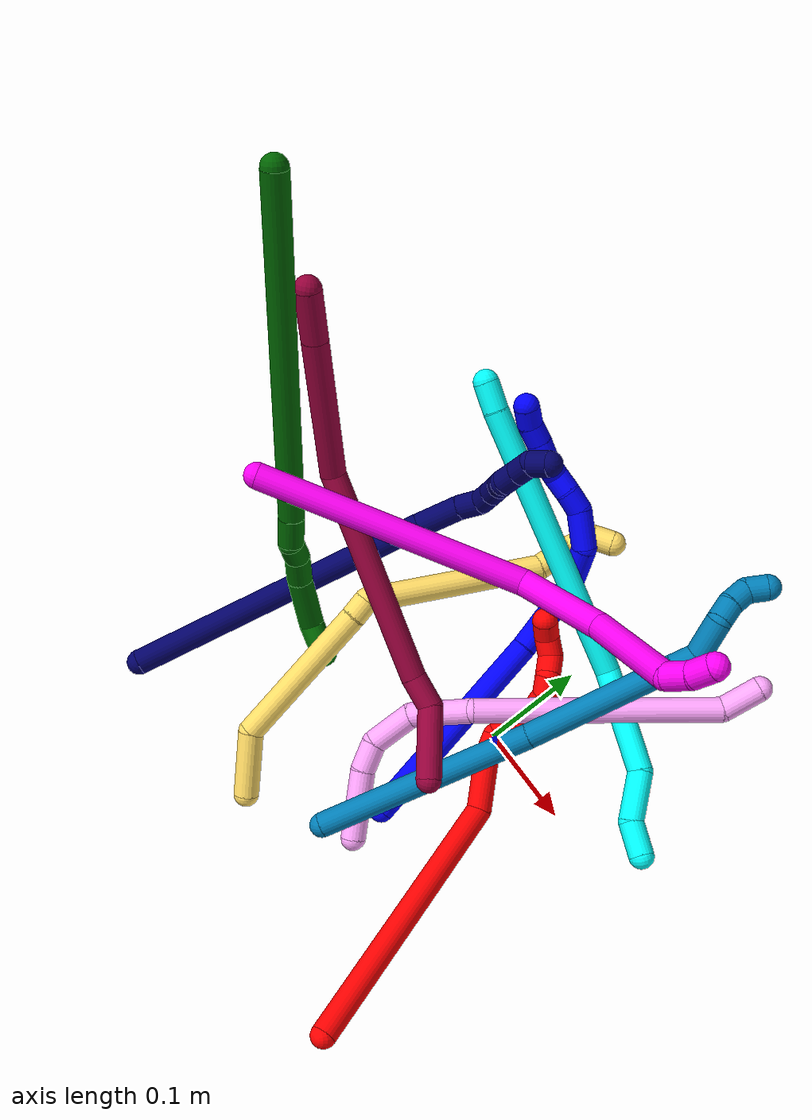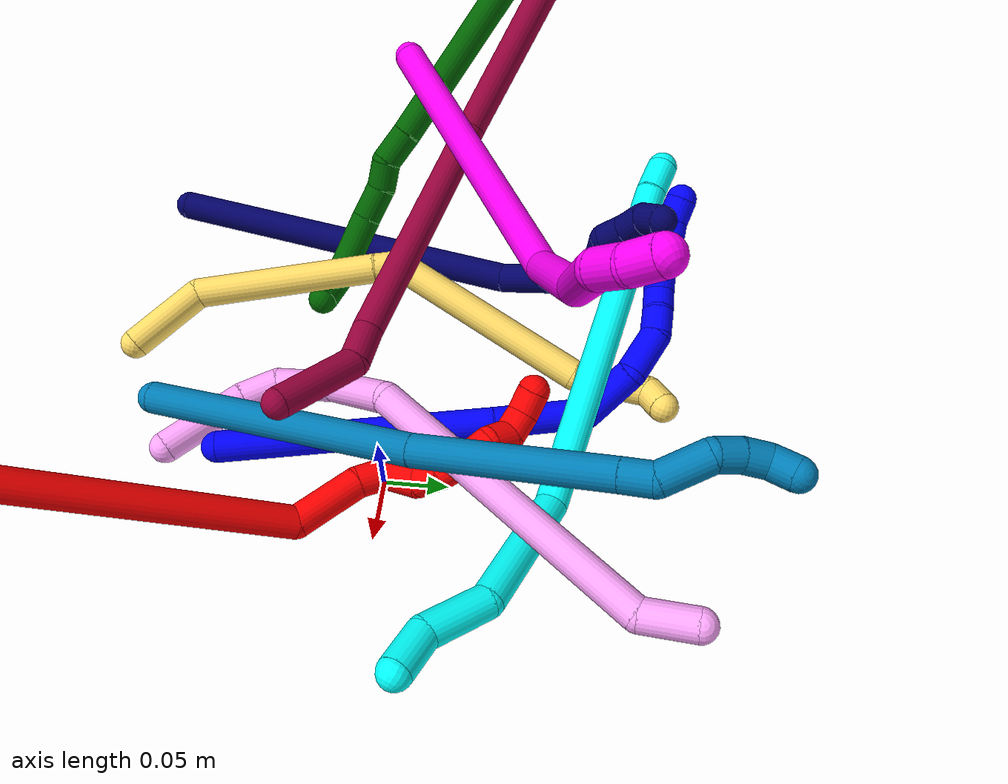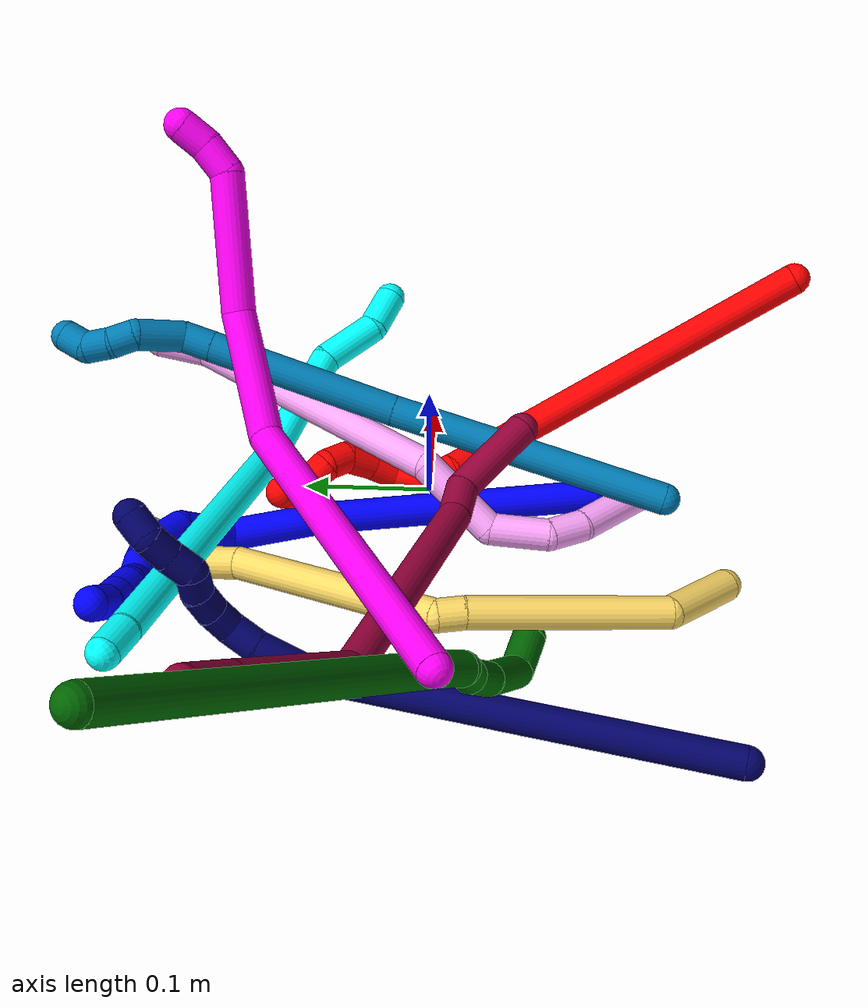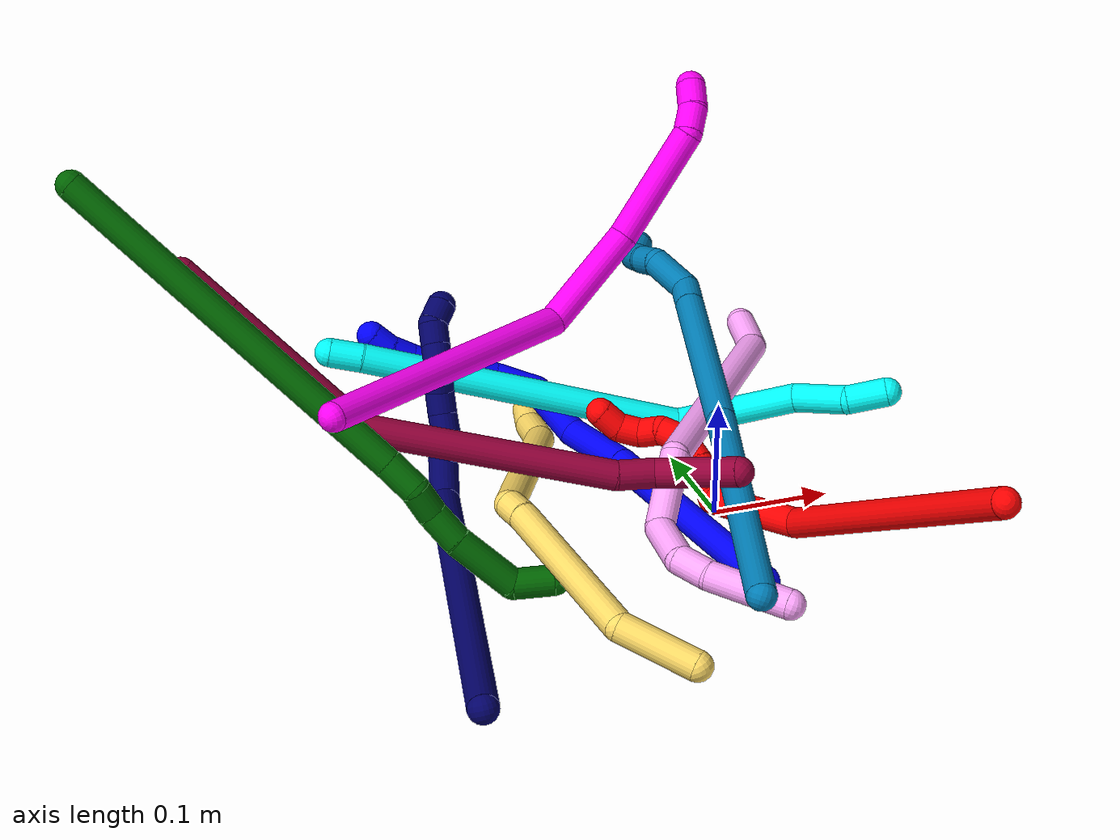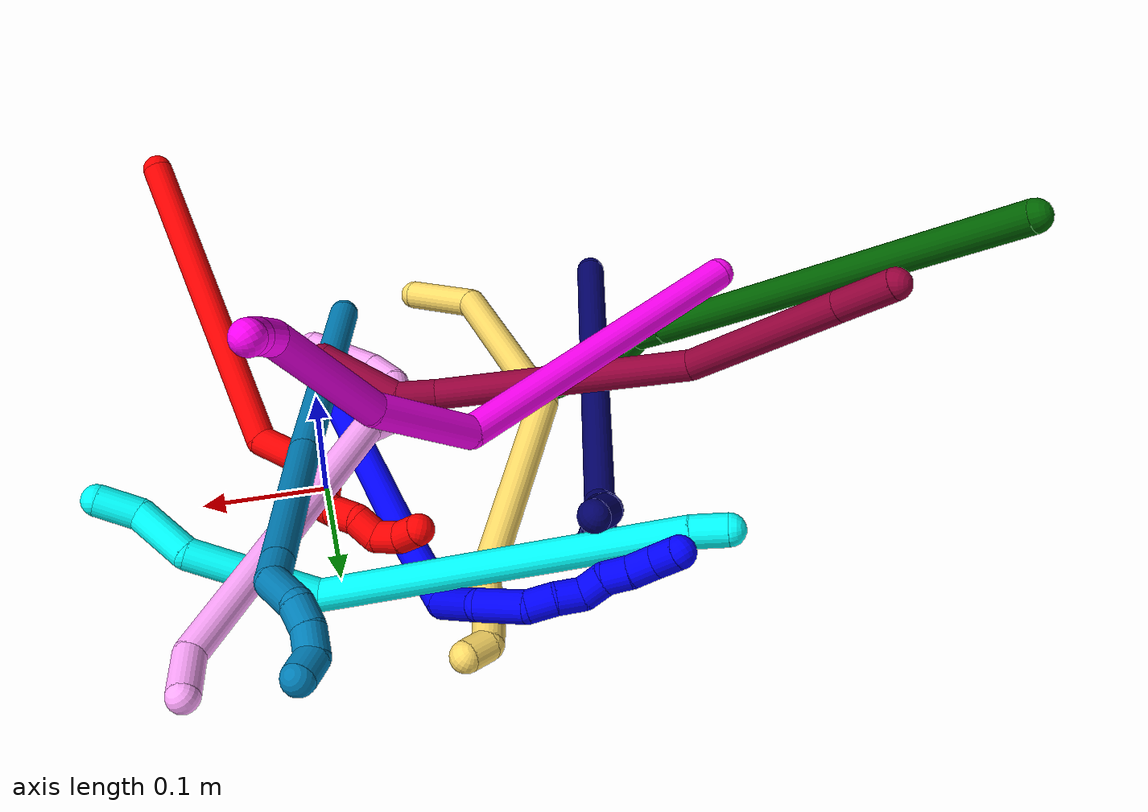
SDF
<sdf version="1.7">
 <world name="default">
  <plugin name="TubeGeneratorPlugin" filename="libtube_generator_plugin.so"/>
  <model name="photoneo_s_sensor">
   <static>1</static>
   <pose>0 0 2 1.57079 1.57079 3.14159</pose>
   <link name="link">
    <inertial><mass>0.1</mass></inertial>
    <sensor name="sensor" type="depth">
     <update_rate>30</update_rate>
     <camera>
      <horizontal_fov>1.22</horizontal_fov>
      <image><width>1920</width><height>1200</height><format>B8G8R8</format></image>
      <clip><near>0.1</near><far>4</far></clip>
      <depth_camera><output>points</output></depth_camera>
     </camera>
     <plugin name="camera_plugin" filename="libgazebo_ros_depth_camera.so">
      <baseline>0.2</baseline>
      <alwaysOn>1</alwaysOn>
      <updateRate>0.0</updateRate>
      <cameraName>camera_ir</cameraName>
      <imageTopicName>/camera/color/image_raw</imageTopicName>
      <cameraInfoTopicName>/camera/color/camera_info</cameraInfoTopicName>
      <depthImageTopicName>/camera/depth/image_raw</depthImageTopicName>
      <depthImageCameraInfoTopicName>/camera/depth/camera_info</depthImageCameraInfoTopicName>
      <pointCloudTopicName>/camera/depth/points</pointCloudTopicName>
      <frameName>fr_optical</frameName>
      <pointCloudCutoff>0.1</pointCloudCutoff>
      <pointCloudCutoffMax>2.0</pointCloudCutoffMax>
      <distortionK1>0</distortionK1>
      <distortionK2>0</distortionK2>
      <distortionK3>0</distortionK3>
      <distortionT1>0</distortionT1>
      <distortionT2>0</distortionT2>
      <CxPrime>0</CxPrime>
      <Cx>0</Cx>
      <Cy>0</Cy>
      <focalLength>0</focalLength>
      <hackBaseline>0</hackBaseline>
     </plugin>
    </sensor>
   </link>
  </model>
  <gravity>0 0 -9.8</gravity>
  <magnetic_field>6e-06 2.3e-05 -4.2e-05</magnetic_field>
  <atmosphere type="adiabatic"/>
  <physics name="default_physics" default="0" type="ode">
   <max_step_size>0.003</max_step_size>
   <real_time_factor>1</real_time_factor>
   <real_time_update_rate>1000</real_time_update_rate>
   <max_contacts>10000</max_contacts>
   <ode>
    <solver>
     <type>quick</type>
     <iters>100</iters>
     <sor>1.3</sor>
     <use_dynamic_moi_rescaling>0</use_dynamic_moi_rescaling>
    </solver>
    <constraints>
     <contact_max_correcting_vel>0</contact_max_correcting_vel>
     <contact_surface_layer>0.001</contact_surface_layer>
     <cfm>0</cfm>
     <erp>0.2</erp>
    </constraints>
   </ode>
  </physics>
  <scene><ambient>0.4 0.4 0.4 1</ambient><background>0.7 0.7 0.7 1</background><shadows>0</shadows></scene>
  <audio><device>default</device></audio>
  <spherical_coordinates>
   <surface_model>EARTH_WGS84</surface_model>
   <latitude_deg>0</latitude_deg>
   <longitude_deg>0</longitude_deg>
   <elevation>0</elevation>
   <heading_deg>0</heading_deg>
  </spherical_coordinates>
  <model name="bin">
   <static>1</static>
   <link name="bottom">
    <collision name="collision-bottom">
     <pose>0 0 -0.01 0 -0 0</pose>
     <geometry><box><size>0.8 0.6 0.02</size></box></geometry>
     <surface>
      <friction><ode><mu>100</mu><mu2>100</mu2></ode></friction>
      <contact><collide_bitmask>65535</collide_bitmask></contact>
     </surface>
    </collision>
   </link>
   <link name="west_wall">
    <collision name="collision-west_wall">
     <pose>-0.41 0 0.1 0 -0 0</pose>
     <geometry><box><size>0.02 0.6 0.2</size></box></geometry>
     <surface>
      <friction><ode><mu>100</mu><mu2>100</mu2></ode></friction>
      <contact><collide_bitmask>65535</collide_bitmask></contact>
     </surface>
    </collision>
   </link>
   <link name="east_wall">
    <collision name="collision-east_wall">
     <pose>0.41 0 0.1 0 -0 0</pose>
     <geometry><box><size>0.02 0.6 0.2</size></box></geometry>
     <surface>
      <friction><ode><mu>100</mu><mu2>100</mu2></ode></friction>
      <contact><collide_bitmask>65535</collide_bitmask></contact>
     </surface>
    </collision>
   </link>
   <link name="south_wall">
    <collision name="collision-south_wall">
     <pose>0 -0.31 0.1 0 -0 0</pose>
     <geometry><box><size>0.8 0.02 0.2</size></box></geometry>
     <surface>
      <friction><ode><mu>100</mu><mu2>100</mu2></ode></friction>
      <contact><collide_bitmask>65535</collide_bitmask></contact>
     </surface>
    </collision>
   </link>
   <link name="north_wall">
    <collision name="collision-north_wall">
     <pose>0 0.31 0.1 0 -0 0</pose>
     <geometry><box><size>0.8 0.02 0.2</size></box></geometry>
     <surface>
      <friction><ode><mu>100</mu><mu2>100</mu2></ode></friction>
      <contact><collide_bitmask>65535</collide_bitmask></contact>
     </surface>
    </collision>
   </link>
  </model>
  <model name="1">
   <static>0</static>
   <link name="1">
    <collision name="collision-cylinder-e_1_1_4">
     <pose>-0.025765 0.056963 0.087995 -0.574509 -0.241015 0.071518</pose>
     <geometry><cylinder><radius>0.0125</radius><length>0.215887</length></cylinder></geometry>
     <surface>
      <friction><ode><mu>1.16</mu><mu2>1.16</mu2><slip1>0</slip1><slip2>0</slip2></ode></friction>
      <contact><ode><kp>1e+06</kp><kd>1</kd><max_vel>0</max_vel><min_depth>0.001</min_depth></ode></contact>
     </surface>
    </collision>
    <visual name="visual-cylinder-e_1_1_4">
     <pose>-0.025765 0.056963 0.087995 -0.574509 -0.241015 0.071518</pose>
     <geometry><cylinder><radius>0.0125</radius><length>0.215887</length></cylinder></geometry>
     <material><ambient>0 0 1 1</ambient></material>
    </visual>
    <collision name="collision-cylinder-e_2_4_5">
     <pose>-0.058262 0.131565 0.208418 -0.498172 -0.180398 0.046004</pose>
     <geometry><cylinder><radius>0.0125</radius><length>0.075047</length></cylinder></geometry>
     <surface>
      <friction><ode><mu>1.16</mu><mu2>1.16</mu2><slip1>0</slip1><slip2>0</slip2></ode></friction>
      <contact><ode><kp>1e+06</kp><kd>1</kd><max_vel>0</max_vel><min_depth>0.001</min_depth></ode></contact>
     </surface>
    </collision>
    <visual name="visual-cylinder-e_2_4_5">
     <pose>-0.058262 0.131565 0.208418 -0.498172 -0.180398 0.046004</pose>
     <geometry><cylinder><radius>0.0125</radius><length>0.075047</length></cylinder></geometry>
     <material><ambient>0 0 1 1</ambient></material>
    </visual>
    <collision name="collision-cylinder-e_3_5_6">
     <pose>-0.060942 0.171129 0.250162 -1.16899 0.168531 -0.111651</pose>
     <geometry><cylinder><radius>0.0125</radius><length>0.048329</length></cylinder></geometry>
     <surface>
      <friction><ode><mu>1.16</mu><mu2>1.16</mu2><slip1>0</slip1><slip2>0</slip2></ode></friction>
      <contact><ode><kp>1e+06</kp><kd>1</kd><max_vel>0</max_vel><min_depth>0.001</min_depth></ode></contact>
     </surface>
    </collision>
    <visual name="visual-cylinder-e_3_5_6">
     <pose>-0.060942 0.171129 0.250162 -1.16899 0.168531 -0.111651</pose>
     <geometry><cylinder><radius>0.0125</radius><length>0.048329</length></cylinder></geometry>
     <material><ambient>0 0 1 1</ambient></material>
    </visual>
    <collision name="collision-cylinder-e_4_6_7">
     <pose>-0.045491 0.204394 0.27017 -0.814819 0.631382 -0.280059</pose>
     <geometry><cylinder><radius>0.0125</radius><length>0.038617</length></cylinder></geometry>
     <surface>
      <friction><ode><mu>1.16</mu><mu2>1.16</mu2><slip1>0</slip1><slip2>0</slip2></ode></friction>
      <contact><ode><kp>1e+06</kp><kd>1</kd><max_vel>0</max_vel><min_depth>0.001</min_depth></ode></contact>
     </surface>
    </collision>
    <visual name="visual-cylinder-e_4_6_7">
     <pose>-0.045491 0.204394 0.27017 -0.814819 0.631382 -0.280059</pose>
     <geometry><cylinder><radius>0.0125</radius><length>0.038617</length></cylinder></geometry>
     <material><ambient>0 0 1 1</ambient></material>
    </visual>
    <collision name="collision-cylinder-e_5_7_8">
     <pose>-0.024791 0.219968 0.283955 -0.939923 1.05769 -0.577056</pose>
     <geometry><cylinder><radius>0.0125</radius><length>0.021357</length></cylinder></geometry>
     <surface>
      <friction><ode><mu>1.16</mu><mu2>1.16</mu2><slip1>0</slip1><slip2>0</slip2></ode></friction>
      <contact><ode><kp>1e+06</kp><kd>1</kd><max_vel>0</max_vel><min_depth>0.001</min_depth></ode></contact>
     </surface>
    </collision>
    <visual name="visual-cylinder-e_5_7_8">
     <pose>-0.024791 0.219968 0.283955 -0.939923 1.05769 -0.577056</pose>
     <geometry><cylinder><radius>0.0125</radius><length>0.021357</length></cylinder></geometry>
     <material><ambient>0 0 1 1</ambient></material>
    </visual>
    <collision name="collision-cylinder-e_6_8_9">
     <pose>-0.006308 0.226517 0.290979 -0.53226 1.10939 -0.334633</pose>
     <geometry><cylinder><radius>0.0125</radius><length>0.020503</length></cylinder></geometry>
     <surface>
      <friction><ode><mu>1.16</mu><mu2>1.16</mu2><slip1>0</slip1><slip2>0</slip2></ode></friction>
      <contact><ode><kp>1e+06</kp><kd>1</kd><max_vel>0</max_vel><min_depth>0.001</min_depth></ode></contact>
     </surface>
    </collision>
    <visual name="visual-cylinder-e_6_8_9">
     <pose>-0.006308 0.226517 0.290979 -0.53226 1.10939 -0.334633</pose>
     <geometry><cylinder><radius>0.0125</radius><length>0.020503</length></cylinder></geometry>
     <material><ambient>0 0 1 1</ambient></material>
    </visual>
    <collision name="collision-cylinder-e_7_9_10">
     <pose>0.010349 0.235634 0.294661 -1.60768 0.832442 -0.860067</pose>
     <geometry><cylinder><radius>0.0125</radius><length>0.020221</length></cylinder></geometry>
     <surface>
      <friction><ode><mu>1.16</mu><mu2>1.16</mu2><slip1>0</slip1><slip2>0</slip2></ode></friction>
      <contact><ode><kp>1e+06</kp><kd>1</kd><max_vel>0</max_vel><min_depth>0.001</min_depth></ode></contact>
     </surface>
    </collision>
    <visual name="visual-cylinder-e_7_9_10">
     <pose>0.010349 0.235634 0.294661 -1.60768 0.832442 -0.860067</pose>
     <geometry><cylinder><radius>0.0125</radius><length>0.020221</length></cylinder></geometry>
     <material><ambient>0 0 1 1</ambient></material>
    </visual>
    <collision name="collision-cylinder-e_8_10_11">
     <pose>0.025194 0.248355 0.297687 -1.06522 0.827784 -0.506704</pose>
     <geometry><cylinder><radius>0.0125</radius><length>0.020007</length></cylinder></geometry>
     <surface>
      <friction><ode><mu>1.16</mu><mu2>1.16</mu2><slip1>0</slip1><slip2>0</slip2></ode></friction>
      <contact><ode><kp>1e+06</kp><kd>1</kd><max_vel>0</max_vel><min_depth>0.001</min_depth></ode></contact>
     </surface>
    </collision>
    <visual name="visual-cylinder-e_8_10_11">
     <pose>0.025194 0.248355 0.297687 -1.06522 0.827784 -0.506704</pose>
     <geometry><cylinder><radius>0.0125</radius><length>0.020007</length></cylinder></geometry>
     <material><ambient>0 0 1 1</ambient></material>
    </visual>
    <collision name="collision-cylinder-e_9_11_12">
     <pose>0.040301 0.260347 0.302847 -1.27025 0.883306 -0.670591</pose>
     <geometry><cylinder><radius>0.0125</radius><length>0.020029</length></cylinder></geometry>
     <surface>
      <friction><ode><mu>1.16</mu><mu2>1.16</mu2><slip1>0</slip1><slip2>0</slip2></ode></friction>
      <contact><ode><kp>1e+06</kp><kd>1</kd><max_vel>0</max_vel><min_depth>0.001</min_depth></ode></contact>
     </surface>
    </collision>
    <visual name="visual-cylinder-e_9_11_12">
     <pose>0.040301 0.260347 0.302847 -1.27025 0.883306 -0.670591</pose>
     <geometry><cylinder><radius>0.0125</radius><length>0.020029</length></cylinder></geometry>
     <material><ambient>0 0 1 1</ambient></material>
    </visual>
    <collision name="collision-cylinder-e_10_12_2">
     <pose>0.053666 0.274464 0.306631 -1.33862 0.597466 -0.477942</pose>
     <geometry><cylinder><radius>0.0125</radius><length>0.020002</length></cylinder></geometry>
     <surface>
      <friction><ode><mu>1.16</mu><mu2>1.16</mu2><slip1>0</slip1><slip2>0</slip2></ode></friction>
      <contact><ode><kp>1e+06</kp><kd>1</kd><max_vel>0</max_vel><min_depth>0.001</min_depth></ode></contact>
     </surface>
    </collision>
    <visual name="visual-cylinder-e_10_12_2">
     <pose>0.053666 0.274464 0.306631 -1.33862 0.597466 -0.477942</pose>
     <geometry><cylinder><radius>0.0125</radius><length>0.020002</length></cylinder></geometry>
     <material><ambient>0 0 1 1</ambient></material>
    </visual>
    <collision name="collision-sphere-2">
     <pose>0.059292 0.28251 0.308533 0 -0 0</pose>
     <geometry><sphere><radius>0.0125</radius></sphere></geometry>
     <surface>
      <friction><ode><mu>1.16</mu><mu2>1.16</mu2><slip1>0</slip1><slip2>0</slip2></ode></friction>
      <contact><ode><kp>1e+06</kp><kd>1</kd><max_vel>0</max_vel><min_depth>0.001</min_depth></ode></contact>
     </surface>
    </collision>
    <visual name="visual-sphere-2">
     <pose>0.059292 0.28251 0.308533 0 -0 0</pose>
     <geometry><sphere><radius>0.0125</radius></sphere></geometry>
     <material><ambient>0 0 1 1</ambient></material>
    </visual>
    <collision name="collision-sphere-12">
     <pose>0.04804 0.266417 0.304728 0 -0 0</pose>
     <geometry><sphere><radius>0.0125</radius></sphere></geometry>
     <surface>
      <friction><ode><mu>1.16</mu><mu2>1.16</mu2><slip1>0</slip1><slip2>0</slip2></ode></friction>
      <contact><ode><kp>1e+06</kp><kd>1</kd><max_vel>0</max_vel><min_depth>0.001</min_depth></ode></contact>
     </surface>
    </collision>
    <visual name="visual-sphere-12">
     <pose>0.04804 0.266417 0.304728 0 -0 0</pose>
     <geometry><sphere><radius>0.0125</radius></sphere></geometry>
     <material><ambient>0 0 1 1</ambient></material>
    </visual>
    <collision name="collision-sphere-11">
     <pose>0.032561 0.254276 0.300965 0 -0 0</pose>
     <geometry><sphere><radius>0.0125</radius></sphere></geometry>
     <surface>
      <friction><ode><mu>1.16</mu><mu2>1.16</mu2><slip1>0</slip1><slip2>0</slip2></ode></friction>
      <contact><ode><kp>1e+06</kp><kd>1</kd><max_vel>0</max_vel><min_depth>0.001</min_depth></ode></contact>
     </surface>
    </collision>
    <visual name="visual-sphere-11">
     <pose>0.032561 0.254276 0.300965 0 -0 0</pose>
     <geometry><sphere><radius>0.0125</radius></sphere></geometry>
     <material><ambient>0 0 1 1</ambient></material>
    </visual>
    <collision name="collision-sphere-10">
     <pose>0.017827 0.242434 0.29441 0 -0 0</pose>
     <geometry><sphere><radius>0.0125</radius></sphere></geometry>
     <surface>
      <friction><ode><mu>1.16</mu><mu2>1.16</mu2><slip1>0</slip1><slip2>0</slip2></ode></friction>
      <contact><ode><kp>1e+06</kp><kd>1</kd><max_vel>0</max_vel><min_depth>0.001</min_depth></ode></contact>
     </surface>
    </collision>
    <visual name="visual-sphere-10">
     <pose>0.017827 0.242434 0.29441 0 -0 0</pose>
     <geometry><sphere><radius>0.0125</radius></sphere></geometry>
     <material><ambient>0 0 1 1</ambient></material>
    </visual>
    <collision name="collision-sphere-9">
     <pose>0.002872 0.228833 0.294912 0 -0 0</pose>
     <geometry><sphere><radius>0.0125</radius></sphere></geometry>
     <surface>
      <friction><ode><mu>1.16</mu><mu2>1.16</mu2><slip1>0</slip1><slip2>0</slip2></ode></friction>
      <contact><ode><kp>1e+06</kp><kd>1</kd><max_vel>0</max_vel><min_depth>0.001</min_depth></ode></contact>
     </surface>
    </collision>
    <visual name="visual-sphere-9">
     <pose>0.002872 0.228833 0.294912 0 -0 0</pose>
     <geometry><sphere><radius>0.0125</radius></sphere></geometry>
     <material><ambient>0 0 1 1</ambient></material>
    </visual>
    <collision name="collision-sphere-4">
     <pose>-0.05153 0.113927 0.17599 0 -0 0</pose>
     <geometry><sphere><radius>0.0125</radius></sphere></geometry>
     <surface>
      <friction><ode><mu>1.16</mu><mu2>1.16</mu2><slip1>0</slip1><slip2>0</slip2></ode></friction>
      <contact><ode><kp>1e+06</kp><kd>1</kd><max_vel>0</max_vel><min_depth>0.001</min_depth></ode></contact>
     </surface>
    </collision>
    <visual name="visual-sphere-4">
     <pose>-0.05153 0.113927 0.17599 0 -0 0</pose>
     <geometry><sphere><radius>0.0125</radius></sphere></geometry>
     <material><ambient>0 0 1 1</ambient></material>
    </visual>
    <collision name="collision-sphere-1">
     <geometry><sphere><radius>0.0125</radius></sphere></geometry>
     <surface>
      <friction><ode><mu>1.16</mu><mu2>1.16</mu2><slip1>0</slip1><slip2>0</slip2></ode></friction>
      <contact><ode><kp>1e+06</kp><kd>1</kd><max_vel>0</max_vel><min_depth>0.001</min_depth></ode></contact>
     </surface>
    </collision>
    <visual name="visual-sphere-1">
     <geometry><sphere><radius>0.0125</radius></sphere></geometry>
     <material><ambient>0 0 1 1</ambient></material>
    </visual>
    <collision name="collision-sphere-8">
     <pose>-0.015487 0.224201 0.287047 0 -0 0</pose>
     <geometry><sphere><radius>0.0125</radius></sphere></geometry>
     <surface>
      <friction><ode><mu>1.16</mu><mu2>1.16</mu2><slip1>0</slip1><slip2>0</slip2></ode></friction>
      <contact><ode><kp>1e+06</kp><kd>1</kd><max_vel>0</max_vel><min_depth>0.001</min_depth></ode></contact>
     </surface>
    </collision>
    <visual name="visual-sphere-8">
     <pose>-0.015487 0.224201 0.287047 0 -0 0</pose>
     <geometry><sphere><radius>0.0125</radius></sphere></geometry>
     <material><ambient>0 0 1 1</ambient></material>
    </visual>
    <collision name="collision-sphere-5">
     <pose>-0.064995 0.149204 0.240846 0 -0 0</pose>
     <geometry><sphere><radius>0.0125</radius></sphere></geometry>
     <surface>
      <friction><ode><mu>1.16</mu><mu2>1.16</mu2><slip1>0</slip1><slip2>0</slip2></ode></friction>
      <contact><ode><kp>1e+06</kp><kd>1</kd><max_vel>0</max_vel><min_depth>0.001</min_depth></ode></contact>
     </surface>
    </collision>
    <visual name="visual-sphere-5">
     <pose>-0.064995 0.149204 0.240846 0 -0 0</pose>
     <geometry><sphere><radius>0.0125</radius></sphere></geometry>
     <material><ambient>0 0 1 1</ambient></material>
    </visual>
    <collision name="collision-sphere-6">
     <pose>-0.056888 0.193054 0.259478 0 -0 0</pose>
     <geometry><sphere><radius>0.0125</radius></sphere></geometry>
     <surface>
      <friction><ode><mu>1.16</mu><mu2>1.16</mu2><slip1>0</slip1><slip2>0</slip2></ode></friction>
      <contact><ode><kp>1e+06</kp><kd>1</kd><max_vel>0</max_vel><min_depth>0.001</min_depth></ode></contact>
     </surface>
    </collision>
    <visual name="visual-sphere-6">
     <pose>-0.056888 0.193054 0.259478 0 -0 0</pose>
     <geometry><sphere><radius>0.0125</radius></sphere></geometry>
     <material><ambient>0 0 1 1</ambient></material>
    </visual>
    <collision name="collision-sphere-7">
     <pose>-0.034094 0.215735 0.280863 0 -0 0</pose>
     <geometry><sphere><radius>0.0125</radius></sphere></geometry>
     <surface>
      <friction><ode><mu>1.16</mu><mu2>1.16</mu2><slip1>0</slip1><slip2>0</slip2></ode></friction>
      <contact><ode><kp>1e+06</kp><kd>1</kd><max_vel>0</max_vel><min_depth>0.001</min_depth></ode></contact>
     </surface>
    </collision>
    <visual name="visual-sphere-7">
     <pose>-0.034094 0.215735 0.280863 0 -0 0</pose>
     <geometry><sphere><radius>0.0125</radius></sphere></geometry>
     <material><ambient>0 0 1 1</ambient></material>
    </visual>
    <inertial>
     <pose>-0.025403 0.13623 0.18661 0 -0 0</pose>
     <mass>0.5</mass>
     <inertia>
      <ixx>0.000938</ixx>
      <ixy>0</ixy>
      <ixz>0</ixz>
      <iyy>0.000843</iyy>
      <iyz>0</iyz>
      <izz>-0.000263</izz>
     </inertia>
    </inertial>
   </link>
   <pose>-0.012626 -0.132421 0.011499 2.10982 -0.068126 -2.71179</pose>
  </model>
  <model name="2">
   <static>0</static>
   <link name="2">
    <collision name="collision-cylinder-e_1_1_4">
     <pose>-0.055804 0.05668 -0.109234 -2.66295 -0.425722 1.44984</pose>
     <geometry><cylinder><radius>0.0125</radius><length>0.27025</length></cylinder></geometry>
     <surface>
      <friction><ode><mu>1.16</mu><mu2>1.16</mu2><slip1>0</slip1><slip2>0</slip2></ode></friction>
      <contact><ode><kp>1e+06</kp><kd>1</kd><max_vel>0</max_vel><min_depth>0.001</min_depth></ode></contact>
     </surface>
    </collision>
    <visual name="visual-cylinder-e_1_1_4">
     <pose>-0.055804 0.05668 -0.109234 -2.66295 -0.425722 1.44984</pose>
     <geometry><cylinder><radius>0.0125</radius><length>0.27025</length></cylinder></geometry>
     <material><ambient>1 0 0 1</ambient></material>
    </visual>
    <collision name="collision-cylinder-e_2_4_5">
     <pose>-0.126371 0.135037 -0.224463 -1.84061 -0.580877 0.748519</pose>
     <geometry><cylinder><radius>0.0125</radius><length>0.053807</length></cylinder></geometry>
     <surface>
      <friction><ode><mu>1.16</mu><mu2>1.16</mu2><slip1>0</slip1><slip2>0</slip2></ode></friction>
      <contact><ode><kp>1e+06</kp><kd>1</kd><max_vel>0</max_vel><min_depth>0.001</min_depth></ode></contact>
     </surface>
    </collision>
    <visual name="visual-cylinder-e_2_4_5">
     <pose>-0.126371 0.135037 -0.224463 -1.84061 -0.580877 0.748519</pose>
     <geometry><cylinder><radius>0.0125</radius><length>0.053807</length></cylinder></geometry>
     <material><ambient>1 0 0 1</ambient></material>
    </visual>
    <collision name="collision-cylinder-e_3_5_6">
     <pose>-0.146359 0.165475 -0.23595 -2.13067 -0.467871 0.813199</pose>
     <geometry><cylinder><radius>0.0125</radius><length>0.023171</length></cylinder></geometry>
     <surface>
      <friction><ode><mu>1.16</mu><mu2>1.16</mu2><slip1>0</slip1><slip2>0</slip2></ode></friction>
      <contact><ode><kp>1e+06</kp><kd>1</kd><max_vel>0</max_vel><min_depth>0.001</min_depth></ode></contact>
     </surface>
    </collision>
    <visual name="visual-cylinder-e_3_5_6">
     <pose>-0.146359 0.165475 -0.23595 -2.13067 -0.467871 0.813199</pose>
     <geometry><cylinder><radius>0.0125</radius><length>0.023171</length></cylinder></geometry>
     <material><ambient>1 0 0 1</ambient></material>
    </visual>
    <collision name="collision-cylinder-e_4_6_7">
     <pose>-0.148529 0.182412 -0.250941 -2.43099 0.239041 -0.626034</pose>
     <geometry><cylinder><radius>0.0125</radius><length>0.0258</length></cylinder></geometry>
     <surface>
      <friction><ode><mu>1.16</mu><mu2>1.16</mu2><slip1>0</slip1><slip2>0</slip2></ode></friction>
      <contact><ode><kp>1e+06</kp><kd>1</kd><max_vel>0</max_vel><min_depth>0.001</min_depth></ode></contact>
     </surface>
    </collision>
    <visual name="visual-cylinder-e_4_6_7">
     <pose>-0.148529 0.182412 -0.250941 -2.43099 0.239041 -0.626034</pose>
     <geometry><cylinder><radius>0.0125</radius><length>0.0258</length></cylinder></geometry>
     <material><ambient>1 0 0 1</ambient></material>
    </visual>
    <collision name="collision-cylinder-e_5_7_8">
     <pose>-0.14301 0.201345 -0.262805 -1.78715 0.220135 -0.273173</pose>
     <geometry><cylinder><radius>0.0125</radius><length>0.022574</length></cylinder></geometry>
     <surface>
      <friction><ode><mu>1.16</mu><mu2>1.16</mu2><slip1>0</slip1><slip2>0</slip2></ode></friction>
      <contact><ode><kp>1e+06</kp><kd>1</kd><max_vel>0</max_vel><min_depth>0.001</min_depth></ode></contact>
     </surface>
    </collision>
    <visual name="visual-cylinder-e_5_7_8">
     <pose>-0.14301 0.201345 -0.262805 -1.78715 0.220135 -0.273173</pose>
     <geometry><cylinder><radius>0.0125</radius><length>0.022574</length></cylinder></geometry>
     <material><ambient>1 0 0 1</ambient></material>
    </visual>
    <collision name="collision-cylinder-e_6_8_9">
     <pose>-0.139883 0.223964 -0.266607 -1.69142 0.055409 -0.062526</pose>
     <geometry><cylinder><radius>0.0125</radius><length>0.023932</length></cylinder></geometry>
     <surface>
      <friction><ode><mu>1.16</mu><mu2>1.16</mu2><slip1>0</slip1><slip2>0</slip2></ode></friction>
      <contact><ode><kp>1e+06</kp><kd>1</kd><max_vel>0</max_vel><min_depth>0.001</min_depth></ode></contact>
     </surface>
    </collision>
    <visual name="visual-cylinder-e_6_8_9">
     <pose>-0.139883 0.223964 -0.266607 -1.69142 0.055409 -0.062526</pose>
     <geometry><cylinder><radius>0.0125</radius><length>0.023932</length></cylinder></geometry>
     <material><ambient>1 0 0 1</ambient></material>
    </visual>
    <collision name="collision-cylinder-e_7_9_10">
     <pose>-0.143989 0.244646 -0.269354 -1.71808 -0.490996 0.565375</pose>
     <geometry><cylinder><radius>0.0125</radius><length>0.020225</length></cylinder></geometry>
     <surface>
      <friction><ode><mu>1.16</mu><mu2>1.16</mu2><slip1>0</slip1><slip2>0</slip2></ode></friction>
      <contact><ode><kp>1e+06</kp><kd>1</kd><max_vel>0</max_vel><min_depth>0.001</min_depth></ode></contact>
     </surface>
    </collision>
    <visual name="visual-cylinder-e_7_9_10">
     <pose>-0.143989 0.244646 -0.269354 -1.71808 -0.490996 0.565375</pose>
     <geometry><cylinder><radius>0.0125</radius><length>0.020225</length></cylinder></geometry>
     <material><ambient>1 0 0 1</ambient></material>
    </visual>
    <collision name="collision-cylinder-e_8_10_11">
     <pose>-0.155801 0.258759 -0.275455 -2.30686 -0.77872 1.49326</pose>
     <geometry><cylinder><radius>0.0125</radius><length>0.02006</length></cylinder></geometry>
     <surface>
      <friction><ode><mu>1.16</mu><mu2>1.16</mu2><slip1>0</slip1><slip2>0</slip2></ode></friction>
      <contact><ode><kp>1e+06</kp><kd>1</kd><max_vel>0</max_vel><min_depth>0.001</min_depth></ode></contact>
     </surface>
    </collision>
    <visual name="visual-cylinder-e_8_10_11">
     <pose>-0.155801 0.258759 -0.275455 -2.30686 -0.77872 1.49326</pose>
     <geometry><cylinder><radius>0.0125</radius><length>0.02006</length></cylinder></geometry>
     <material><ambient>1 0 0 1</ambient></material>
    </visual>
    <collision name="collision-cylinder-e_9_11_12">
     <pose>-0.169163 0.271671 -0.278752 -1.37694 -0.682848 0.568869</pose>
     <geometry><cylinder><radius>0.0125</radius><length>0.020023</length></cylinder></geometry>
     <surface>
      <friction><ode><mu>1.16</mu><mu2>1.16</mu2><slip1>0</slip1><slip2>0</slip2></ode></friction>
      <contact><ode><kp>1e+06</kp><kd>1</kd><max_vel>0</max_vel><min_depth>0.001</min_depth></ode></contact>
     </surface>
    </collision>
    <visual name="visual-cylinder-e_9_11_12">
     <pose>-0.169163 0.271671 -0.278752 -1.37694 -0.682848 0.568869</pose>
     <geometry><cylinder><radius>0.0125</radius><length>0.020023</length></cylinder></geometry>
     <material><ambient>1 0 0 1</ambient></material>
    </visual>
    <collision name="collision-cylinder-e_10_12_2">
     <pose>-0.177759 0.288269 -0.273279 -1.15378 -0.228027 0.148756</pose>
     <geometry><cylinder><radius>0.0125</radius><length>0.020159</length></cylinder></geometry>
     <surface>
      <friction><ode><mu>1.16</mu><mu2>1.16</mu2><slip1>0</slip1><slip2>0</slip2></ode></friction>
      <contact><ode><kp>1e+06</kp><kd>1</kd><max_vel>0</max_vel><min_depth>0.001</min_depth></ode></contact>
     </surface>
    </collision>
    <visual name="visual-cylinder-e_10_12_2">
     <pose>-0.177759 0.288269 -0.273279 -1.15378 -0.228027 0.148756</pose>
     <geometry><cylinder><radius>0.0125</radius><length>0.020159</length></cylinder></geometry>
     <material><ambient>1 0 0 1</ambient></material>
    </visual>
    <collision name="collision-sphere-2">
     <pose>-0.180038 0.297247 -0.269302 0 -0 0</pose>
     <geometry><sphere><radius>0.0125</radius></sphere></geometry>
     <surface>
      <friction><ode><mu>1.16</mu><mu2>1.16</mu2><slip1>0</slip1><slip2>0</slip2></ode></friction>
      <contact><ode><kp>1e+06</kp><kd>1</kd><max_vel>0</max_vel><min_depth>0.001</min_depth></ode></contact>
     </surface>
    </collision>
    <visual name="visual-sphere-2">
     <pose>-0.180038 0.297247 -0.269302 0 -0 0</pose>
     <geometry><sphere><radius>0.0125</radius></sphere></geometry>
     <material><ambient>1 0 0 1</ambient></material>
    </visual>
    <collision name="collision-sphere-12">
     <pose>-0.175481 0.279292 -0.277256 0 -0 0</pose>
     <geometry><sphere><radius>0.0125</radius></sphere></geometry>
     <surface>
      <friction><ode><mu>1.16</mu><mu2>1.16</mu2><slip1>0</slip1><slip2>0</slip2></ode></friction>
      <contact><ode><kp>1e+06</kp><kd>1</kd><max_vel>0</max_vel><min_depth>0.001</min_depth></ode></contact>
     </surface>
    </collision>
    <visual name="visual-sphere-12">
     <pose>-0.175481 0.279292 -0.277256 0 -0 0</pose>
     <geometry><sphere><radius>0.0125</radius></sphere></geometry>
     <material><ambient>1 0 0 1</ambient></material>
    </visual>
    <collision name="collision-sphere-11">
     <pose>-0.162846 0.26405 -0.280249 0 -0 0</pose>
     <geometry><sphere><radius>0.0125</radius></sphere></geometry>
     <surface>
      <friction><ode><mu>1.16</mu><mu2>1.16</mu2><slip1>0</slip1><slip2>0</slip2></ode></friction>
      <contact><ode><kp>1e+06</kp><kd>1</kd><max_vel>0</max_vel><min_depth>0.001</min_depth></ode></contact>
     </surface>
    </collision>
    <visual name="visual-sphere-11">
     <pose>-0.162846 0.26405 -0.280249 0 -0 0</pose>
     <geometry><sphere><radius>0.0125</radius></sphere></geometry>
     <material><ambient>1 0 0 1</ambient></material>
    </visual>
    <collision name="collision-sphere-10">
     <pose>-0.148757 0.253468 -0.270662 0 -0 0</pose>
     <geometry><sphere><radius>0.0125</radius></sphere></geometry>
     <surface>
      <friction><ode><mu>1.16</mu><mu2>1.16</mu2><slip1>0</slip1><slip2>0</slip2></ode></friction>
      <contact><ode><kp>1e+06</kp><kd>1</kd><max_vel>0</max_vel><min_depth>0.001</min_depth></ode></contact>
     </surface>
    </collision>
    <visual name="visual-sphere-10">
     <pose>-0.148757 0.253468 -0.270662 0 -0 0</pose>
     <geometry><sphere><radius>0.0125</radius></sphere></geometry>
     <material><ambient>1 0 0 1</ambient></material>
    </visual>
    <collision name="collision-sphere-9">
     <pose>-0.13922 0.235825 -0.268045 0 -0 0</pose>
     <geometry><sphere><radius>0.0125</radius></sphere></geometry>
     <surface>
      <friction><ode><mu>1.16</mu><mu2>1.16</mu2><slip1>0</slip1><slip2>0</slip2></ode></friction>
      <contact><ode><kp>1e+06</kp><kd>1</kd><max_vel>0</max_vel><min_depth>0.001</min_depth></ode></contact>
     </surface>
    </collision>
    <visual name="visual-sphere-9">
     <pose>-0.13922 0.235825 -0.268045 0 -0 0</pose>
     <geometry><sphere><radius>0.0125</radius></sphere></geometry>
     <material><ambient>1 0 0 1</ambient></material>
    </visual>
    <collision name="collision-sphere-4">
     <pose>-0.111607 0.11336 -0.218468 0 -0 0</pose>
     <geometry><sphere><radius>0.0125</radius></sphere></geometry>
     <surface>
      <friction><ode><mu>1.16</mu><mu2>1.16</mu2><slip1>0</slip1><slip2>0</slip2></ode></friction>
      <contact><ode><kp>1e+06</kp><kd>1</kd><max_vel>0</max_vel><min_depth>0.001</min_depth></ode></contact>
     </surface>
    </collision>
    <visual name="visual-sphere-4">
     <pose>-0.111607 0.11336 -0.218468 0 -0 0</pose>
     <geometry><sphere><radius>0.0125</radius></sphere></geometry>
     <material><ambient>1 0 0 1</ambient></material>
    </visual>
    <collision name="collision-sphere-1">
     <geometry><sphere><radius>0.0125</radius></sphere></geometry>
     <surface>
      <friction><ode><mu>1.16</mu><mu2>1.16</mu2><slip1>0</slip1><slip2>0</slip2></ode></friction>
      <contact><ode><kp>1e+06</kp><kd>1</kd><max_vel>0</max_vel><min_depth>0.001</min_depth></ode></contact>
     </surface>
    </collision>
    <visual name="visual-sphere-1">
     <geometry><sphere><radius>0.0125</radius></sphere></geometry>
     <material><ambient>1 0 0 1</ambient></material>
    </visual>
    <collision name="collision-sphere-8">
     <pose>-0.140546 0.212103 -0.26517 0 -0 0</pose>
     <geometry><sphere><radius>0.0125</radius></sphere></geometry>
     <surface>
      <friction><ode><mu>1.16</mu><mu2>1.16</mu2><slip1>0</slip1><slip2>0</slip2></ode></friction>
      <contact><ode><kp>1e+06</kp><kd>1</kd><max_vel>0</max_vel><min_depth>0.001</min_depth></ode></contact>
     </surface>
    </collision>
    <visual name="visual-sphere-8">
     <pose>-0.140546 0.212103 -0.26517 0 -0 0</pose>
     <geometry><sphere><radius>0.0125</radius></sphere></geometry>
     <material><ambient>1 0 0 1</ambient></material>
    </visual>
    <collision name="collision-sphere-5">
     <pose>-0.141134 0.156714 -0.230458 0 -0 0</pose>
     <geometry><sphere><radius>0.0125</radius></sphere></geometry>
     <surface>
      <friction><ode><mu>1.16</mu><mu2>1.16</mu2><slip1>0</slip1><slip2>0</slip2></ode></friction>
      <contact><ode><kp>1e+06</kp><kd>1</kd><max_vel>0</max_vel><min_depth>0.001</min_depth></ode></contact>
     </surface>
    </collision>
    <visual name="visual-sphere-5">
     <pose>-0.141134 0.156714 -0.230458 0 -0 0</pose>
     <geometry><sphere><radius>0.0125</radius></sphere></geometry>
     <material><ambient>1 0 0 1</ambient></material>
    </visual>
    <collision name="collision-sphere-6">
     <pose>-0.151584 0.174237 -0.241441 0 -0 0</pose>
     <geometry><sphere><radius>0.0125</radius></sphere></geometry>
     <surface>
      <friction><ode><mu>1.16</mu><mu2>1.16</mu2><slip1>0</slip1><slip2>0</slip2></ode></friction>
      <contact><ode><kp>1e+06</kp><kd>1</kd><max_vel>0</max_vel><min_depth>0.001</min_depth></ode></contact>
     </surface>
    </collision>
    <visual name="visual-sphere-6">
     <pose>-0.151584 0.174237 -0.241441 0 -0 0</pose>
     <geometry><sphere><radius>0.0125</radius></sphere></geometry>
     <material><ambient>1 0 0 1</ambient></material>
    </visual>
    <collision name="collision-sphere-7">
     <pose>-0.145475 0.190587 -0.260441 0 -0 0</pose>
     <geometry><sphere><radius>0.0125</radius></sphere></geometry>
     <surface>
      <friction><ode><mu>1.16</mu><mu2>1.16</mu2><slip1>0</slip1><slip2>0</slip2></ode></friction>
      <contact><ode><kp>1e+06</kp><kd>1</kd><max_vel>0</max_vel><min_depth>0.001</min_depth></ode></contact>
     </surface>
    </collision>
    <visual name="visual-sphere-7">
     <pose>-0.145475 0.190587 -0.260441 0 -0 0</pose>
     <geometry><sphere><radius>0.0125</radius></sphere></geometry>
     <material><ambient>1 0 0 1</ambient></material>
    </visual>
    <inertial>
     <pose>-0.097376 0.124837 -0.175833 0 -0 0</pose>
     <mass>0.5</mass>
     <inertia>
      <ixx>0.001695</ixx>
      <ixy>0</ixy>
      <ixz>0</ixz>
      <iyy>0.001668</iyy>
      <iyz>0</iyz>
      <izz>-4.4e-05</izz>
     </inertia>
    </inertial>
   </link>
   <pose>0.106268 -0.285487 0.142715 0.739153 -0.54938 0.033987</pose>
  </model>
  <model name="3">
   <static>0</static>
   <link name="3">
    <collision name="collision-cylinder-e_1_1_4">
     <pose>0.001653 -0.000907 -0.013918 3.07653 0.117935 2.13402</pose>
     <geometry><cylinder><radius>0.0125</radius><length>0.02809</length></cylinder></geometry>
     <surface>
      <friction><ode><mu>1.16</mu><mu2>1.16</mu2><slip1>0</slip1><slip2>0</slip2></ode></friction>
      <contact><ode><kp>1e+06</kp><kd>1</kd><max_vel>0</max_vel><min_depth>0.001</min_depth></ode></contact>
     </surface>
    </collision>
    <visual name="visual-cylinder-e_1_1_4">
     <pose>0.001653 -0.000907 -0.013918 3.07653 0.117935 2.13402</pose>
     <geometry><cylinder><radius>0.0125</radius><length>0.02809</length></cylinder></geometry>
     <material><ambient>0.003922 1 0.996078 1</ambient></material>
    </visual>
    <collision name="collision-cylinder-e_2_4_5">
     <pose>0.02704 0.00425 -0.167066 -3.09807 0.168689 -2.63763</pose>
     <geometry><cylinder><radius>0.0125</radius><length>0.282737</length></cylinder></geometry>
     <surface>
      <friction><ode><mu>1.16</mu><mu2>1.16</mu2><slip1>0</slip1><slip2>0</slip2></ode></friction>
      <contact><ode><kp>1e+06</kp><kd>1</kd><max_vel>0</max_vel><min_depth>0.001</min_depth></ode></contact>
     </surface>
    </collision>
    <visual name="visual-cylinder-e_2_4_5">
     <pose>0.02704 0.00425 -0.167066 -3.09807 0.168689 -2.63763</pose>
     <geometry><cylinder><radius>0.0125</radius><length>0.282737</length></cylinder></geometry>
     <material><ambient>0.003922 1 0.996078 1</ambient></material>
    </visual>
    <collision name="collision-cylinder-e_3_5_6">
     <pose>0.060299 -0.015155 -0.351054 2.62424 0.182892 0.667214</pose>
     <geometry><cylinder><radius>0.0125</radius><length>0.10474</length></cylinder></geometry>
     <surface>
      <friction><ode><mu>1.16</mu><mu2>1.16</mu2><slip1>0</slip1><slip2>0</slip2></ode></friction>
      <contact><ode><kp>1e+06</kp><kd>1</kd><max_vel>0</max_vel><min_depth>0.001</min_depth></ode></contact>
     </surface>
    </collision>
    <visual name="visual-cylinder-e_3_5_6">
     <pose>0.060299 -0.015155 -0.351054 2.62424 0.182892 0.667214</pose>
     <geometry><cylinder><radius>0.0125</radius><length>0.10474</length></cylinder></geometry>
     <material><ambient>0.003922 1 0.996078 1</ambient></material>
    </visual>
    <collision name="collision-cylinder-e_4_6_7">
     <pose>0.062461 -0.054605 -0.415226 2.51751 -0.298521 -0.872445</pose>
     <geometry><cylinder><radius>0.0125</radius><length>0.050065</length></cylinder></geometry>
     <surface>
      <friction><ode><mu>1.16</mu><mu2>1.16</mu2><slip1>0</slip1><slip2>0</slip2></ode></friction>
      <contact><ode><kp>1e+06</kp><kd>1</kd><max_vel>0</max_vel><min_depth>0.001</min_depth></ode></contact>
     </surface>
    </collision>
    <visual name="visual-cylinder-e_4_6_7">
     <pose>0.062461 -0.054605 -0.415226 2.51751 -0.298521 -0.872445</pose>
     <geometry><cylinder><radius>0.0125</radius><length>0.050065</length></cylinder></geometry>
     <material><ambient>0.003922 1 0.996078 1</ambient></material>
    </visual>
    <collision name="collision-cylinder-e_5_7_2">
     <pose>0.057944 -0.076953 -0.449379 2.62522 0.166307 0.61143</pose>
     <geometry><cylinder><radius>0.0125</radius><length>0.034367</length></cylinder></geometry>
     <surface>
      <friction><ode><mu>1.16</mu><mu2>1.16</mu2><slip1>0</slip1><slip2>0</slip2></ode></friction>
      <contact><ode><kp>1e+06</kp><kd>1</kd><max_vel>0</max_vel><min_depth>0.001</min_depth></ode></contact>
     </surface>
    </collision>
    <visual name="visual-cylinder-e_5_7_2">
     <pose>0.057944 -0.076953 -0.449379 2.62522 0.166307 0.61143</pose>
     <geometry><cylinder><radius>0.0125</radius><length>0.034367</length></cylinder></geometry>
     <material><ambient>0.003922 1 0.996078 1</ambient></material>
    </visual>
    <collision name="collision-sphere-2">
     <pose>0.060788 -0.08532 -0.464116 0 -0 0</pose>
     <geometry><sphere><radius>0.0125</radius></sphere></geometry>
     <surface>
      <friction><ode><mu>1.16</mu><mu2>1.16</mu2><slip1>0</slip1><slip2>0</slip2></ode></friction>
      <contact><ode><kp>1e+06</kp><kd>1</kd><max_vel>0</max_vel><min_depth>0.001</min_depth></ode></contact>
     </surface>
    </collision>
    <visual name="visual-sphere-2">
     <pose>0.060788 -0.08532 -0.464116 0 -0 0</pose>
     <geometry><sphere><radius>0.0125</radius></sphere></geometry>
     <material><ambient>0.003922 1 0.996078 1</ambient></material>
    </visual>
    <collision name="collision-sphere-7">
     <pose>0.055099 -0.068586 -0.434642 0 -0 0</pose>
     <geometry><sphere><radius>0.0125</radius></sphere></geometry>
     <surface>
      <friction><ode><mu>1.16</mu><mu2>1.16</mu2><slip1>0</slip1><slip2>0</slip2></ode></friction>
      <contact><ode><kp>1e+06</kp><kd>1</kd><max_vel>0</max_vel><min_depth>0.001</min_depth></ode></contact>
     </surface>
    </collision>
    <visual name="visual-sphere-7">
     <pose>0.055099 -0.068586 -0.434642 0 -0 0</pose>
     <geometry><sphere><radius>0.0125</radius></sphere></geometry>
     <material><ambient>0.003922 1 0.996078 1</ambient></material>
    </visual>
    <collision name="collision-sphere-6">
     <pose>0.069824 -0.040624 -0.395811 0 -0 0</pose>
     <geometry><sphere><radius>0.0125</radius></sphere></geometry>
     <surface>
      <friction><ode><mu>1.16</mu><mu2>1.16</mu2><slip1>0</slip1><slip2>0</slip2></ode></friction>
      <contact><ode><kp>1e+06</kp><kd>1</kd><max_vel>0</max_vel><min_depth>0.001</min_depth></ode></contact>
     </surface>
    </collision>
    <visual name="visual-sphere-6">
     <pose>0.069824 -0.040624 -0.395811 0 -0 0</pose>
     <geometry><sphere><radius>0.0125</radius></sphere></geometry>
     <material><ambient>0.003922 1 0.996078 1</ambient></material>
    </visual>
    <collision name="collision-sphere-5">
     <pose>0.050774 0.010314 -0.306296 0 -0 0</pose>
     <geometry><sphere><radius>0.0125</radius></sphere></geometry>
     <surface>
      <friction><ode><mu>1.16</mu><mu2>1.16</mu2><slip1>0</slip1><slip2>0</slip2></ode></friction>
      <contact><ode><kp>1e+06</kp><kd>1</kd><max_vel>0</max_vel><min_depth>0.001</min_depth></ode></contact>
     </surface>
    </collision>
    <visual name="visual-sphere-5">
     <pose>0.050774 0.010314 -0.306296 0 -0 0</pose>
     <geometry><sphere><radius>0.0125</radius></sphere></geometry>
     <material><ambient>0.003922 1 0.996078 1</ambient></material>
    </visual>
    <collision name="collision-sphere-1">
     <geometry><sphere><radius>0.0125</radius></sphere></geometry>
     <surface>
      <friction><ode><mu>1.16</mu><mu2>1.16</mu2><slip1>0</slip1><slip2>0</slip2></ode></friction>
      <contact><ode><kp>1e+06</kp><kd>1</kd><max_vel>0</max_vel><min_depth>0.001</min_depth></ode></contact>
     </surface>
    </collision>
    <visual name="visual-sphere-1">
     <geometry><sphere><radius>0.0125</radius></sphere></geometry>
     <material><ambient>0.003922 1 0.996078 1</ambient></material>
    </visual>
    <collision name="collision-sphere-4">
     <pose>0.003305 -0.001814 -0.027836 0 -0 0</pose>
     <geometry><sphere><radius>0.0125</radius></sphere></geometry>
     <surface>
      <friction><ode><mu>1.16</mu><mu2>1.16</mu2><slip1>0</slip1><slip2>0</slip2></ode></friction>
      <contact><ode><kp>1e+06</kp><kd>1</kd><max_vel>0</max_vel><min_depth>0.001</min_depth></ode></contact>
     </surface>
    </collision>
    <visual name="visual-sphere-4">
     <pose>0.003305 -0.001814 -0.027836 0 -0 0</pose>
     <geometry><sphere><radius>0.0125</radius></sphere></geometry>
     <material><ambient>0.003922 1 0.996078 1</ambient></material>
    </visual>
    <inertial>
     <pose>0.038251 -0.011579 -0.241257 0 -0 0</pose>
     <mass>0.5</mass>
     <inertia>
      <ixx>-0.002389</ixx>
      <ixy>0</ixy>
      <ixz>0</ixz>
      <iyy>0.000743</iyy>
      <iyz>0</iyz>
      <izz>-0.000393</izz>
     </inertia>
    </inertial>
   </link>
   <pose>-0.273504 0.202245 0.097118 -1.27875 -0.273561 1.07308</pose>
  </model>
  <model name="4">
   <static>0</static>
   <link name="4">
    <collision name="collision-cylinder-e_1_1_4">
     <pose>-0.006434 -0.019179 0.003758 1.3773 -0.318055 -0.262493</pose>
     <geometry><cylinder><radius>0.0125</radius><length>0.041151</length></cylinder></geometry>
     <surface>
      <friction><ode><mu>1.16</mu><mu2>1.16</mu2><slip1>0</slip1><slip2>0</slip2></ode></friction>
      <contact><ode><kp>1e+06</kp><kd>1</kd><max_vel>0</max_vel><min_depth>0.001</min_depth></ode></contact>
     </surface>
    </collision>
    <visual name="visual-cylinder-e_1_1_4">
     <pose>-0.006434 -0.019179 0.003758 1.3773 -0.318055 -0.262493</pose>
     <geometry><cylinder><radius>0.0125</radius><length>0.041151</length></cylinder></geometry>
     <material><ambient>1 0.65098 0.996078 1</ambient></material>
    </visual>
    <collision name="collision-cylinder-e_2_4_5">
     <pose>0.015176 -0.154122 0.03287 1.35519 0.232379 0.187289</pose>
     <geometry><cylinder><radius>0.0125</radius><length>0.243562</length></cylinder></geometry>
     <surface>
      <friction><ode><mu>1.16</mu><mu2>1.16</mu2><slip1>0</slip1><slip2>0</slip2></ode></friction>
      <contact><ode><kp>1e+06</kp><kd>1</kd><max_vel>0</max_vel><min_depth>0.001</min_depth></ode></contact>
     </surface>
    </collision>
    <visual name="visual-cylinder-e_2_4_5">
     <pose>0.015176 -0.154122 0.03287 1.35519 0.232379 0.187289</pose>
     <geometry><cylinder><radius>0.0125</radius><length>0.243562</length></cylinder></geometry>
     <material><ambient>1 0.65098 0.996078 1</ambient></material>
    </visual>
    <collision name="collision-cylinder-e_3_5_6">
     <pose>0.040672 -0.295935 0.081154 0.849018 -0.073331 -0.033157</pose>
     <geometry><cylinder><radius>0.0125</radius><length>0.069595</length></cylinder></geometry>
     <surface>
      <friction><ode><mu>1.16</mu><mu2>1.16</mu2><slip1>0</slip1><slip2>0</slip2></ode></friction>
      <contact><ode><kp>1e+06</kp><kd>1</kd><max_vel>0</max_vel><min_depth>0.001</min_depth></ode></contact>
     </surface>
    </collision>
    <visual name="visual-cylinder-e_3_5_6">
     <pose>0.040672 -0.295935 0.081154 0.849018 -0.073331 -0.033157</pose>
     <geometry><cylinder><radius>0.0125</radius><length>0.069595</length></cylinder></geometry>
     <material><ambient>1 0.65098 0.996078 1</ambient></material>
    </visual>
    <collision name="collision-cylinder-e_4_6_7">
     <pose>0.028936 -0.342983 0.106311 1.4651 -0.410365 -0.370118</pose>
     <geometry><cylinder><radius>0.0125</radius><length>0.046054</length></cylinder></geometry>
     <surface>
      <friction><ode><mu>1.16</mu><mu2>1.16</mu2><slip1>0</slip1><slip2>0</slip2></ode></friction>
      <contact><ode><kp>1e+06</kp><kd>1</kd><max_vel>0</max_vel><min_depth>0.001</min_depth></ode></contact>
     </surface>
    </collision>
    <visual name="visual-cylinder-e_4_6_7">
     <pose>0.028936 -0.342983 0.106311 1.4651 -0.410365 -0.370118</pose>
     <geometry><cylinder><radius>0.0125</radius><length>0.046054</length></cylinder></geometry>
     <material><ambient>1 0.65098 0.996078 1</ambient></material>
    </visual>
    <collision name="collision-cylinder-e_5_7_8">
     <pose>0.007935 -0.373064 0.10721 1.71601 -0.910202 -1.03029</pose>
     <geometry><cylinder><radius>0.0125</radius><length>0.029924</length></cylinder></geometry>
     <surface>
      <friction><ode><mu>1.16</mu><mu2>1.16</mu2><slip1>0</slip1><slip2>0</slip2></ode></friction>
      <contact><ode><kp>1e+06</kp><kd>1</kd><max_vel>0</max_vel><min_depth>0.001</min_depth></ode></contact>
     </surface>
    </collision>
    <visual name="visual-cylinder-e_5_7_8">
     <pose>0.007935 -0.373064 0.10721 1.71601 -0.910202 -1.03029</pose>
     <geometry><cylinder><radius>0.0125</radius><length>0.029924</length></cylinder></geometry>
     <material><ambient>1 0.65098 0.996078 1</ambient></material>
    </visual>
    <collision name="collision-cylinder-e_6_8_2">
     <pose>-0.035244 -0.396174 0.100008 1.96736 -1.11936 -1.51063</pose>
     <geometry><cylinder><radius>0.0125</radius><length>0.069713</length></cylinder></geometry>
     <surface>
      <friction><ode><mu>1.16</mu><mu2>1.16</mu2><slip1>0</slip1><slip2>0</slip2></ode></friction>
      <contact><ode><kp>1e+06</kp><kd>1</kd><max_vel>0</max_vel><min_depth>0.001</min_depth></ode></contact>
     </surface>
    </collision>
    <visual name="visual-cylinder-e_6_8_2">
     <pose>-0.035244 -0.396174 0.100008 1.96736 -1.11936 -1.51063</pose>
     <geometry><cylinder><radius>0.0125</radius><length>0.069713</length></cylinder></geometry>
     <material><ambient>1 0.65098 0.996078 1</ambient></material>
    </visual>
    <collision name="collision-sphere-2">
     <pose>-0.066609 -0.4102 0.094135 0 -0 0</pose>
     <geometry><sphere><radius>0.0125</radius></sphere></geometry>
     <surface>
      <friction><ode><mu>1.16</mu><mu2>1.16</mu2><slip1>0</slip1><slip2>0</slip2></ode></friction>
      <contact><ode><kp>1e+06</kp><kd>1</kd><max_vel>0</max_vel><min_depth>0.001</min_depth></ode></contact>
     </surface>
    </collision>
    <visual name="visual-sphere-2">
     <pose>-0.066609 -0.4102 0.094135 0 -0 0</pose>
     <geometry><sphere><radius>0.0125</radius></sphere></geometry>
     <material><ambient>1 0.65098 0.996078 1</ambient></material>
    </visual>
    <collision name="collision-sphere-4">
     <pose>-0.012869 -0.038358 0.007516 0 -0 0</pose>
     <geometry><sphere><radius>0.0125</radius></sphere></geometry>
     <surface>
      <friction><ode><mu>1.16</mu><mu2>1.16</mu2><slip1>0</slip1><slip2>0</slip2></ode></friction>
      <contact><ode><kp>1e+06</kp><kd>1</kd><max_vel>0</max_vel><min_depth>0.001</min_depth></ode></contact>
     </surface>
    </collision>
    <visual name="visual-sphere-4">
     <pose>-0.012869 -0.038358 0.007516 0 -0 0</pose>
     <geometry><sphere><radius>0.0125</radius></sphere></geometry>
     <material><ambient>1 0.65098 0.996078 1</ambient></material>
    </visual>
    <collision name="collision-sphere-1">
     <geometry><sphere><radius>0.0125</radius></sphere></geometry>
     <surface>
      <friction><ode><mu>1.16</mu><mu2>1.16</mu2><slip1>0</slip1><slip2>0</slip2></ode></friction>
      <contact><ode><kp>1e+06</kp><kd>1</kd><max_vel>0</max_vel><min_depth>0.001</min_depth></ode></contact>
     </surface>
    </collision>
    <visual name="visual-sphere-1">
     <geometry><sphere><radius>0.0125</radius></sphere></geometry>
     <material><ambient>1 0.65098 0.996078 1</ambient></material>
    </visual>
    <collision name="collision-sphere-8">
     <pose>-0.003879 -0.382148 0.105882 0 -0 0</pose>
     <geometry><sphere><radius>0.0125</radius></sphere></geometry>
     <surface>
      <friction><ode><mu>1.16</mu><mu2>1.16</mu2><slip1>0</slip1><slip2>0</slip2></ode></friction>
      <contact><ode><kp>1e+06</kp><kd>1</kd><max_vel>0</max_vel><min_depth>0.001</min_depth></ode></contact>
     </surface>
    </collision>
    <visual name="visual-sphere-8">
     <pose>-0.003879 -0.382148 0.105882 0 -0 0</pose>
     <geometry><sphere><radius>0.0125</radius></sphere></geometry>
     <material><ambient>1 0.65098 0.996078 1</ambient></material>
    </visual>
    <collision name="collision-sphere-5">
     <pose>0.043222 -0.269885 0.058224 0 -0 0</pose>
     <geometry><sphere><radius>0.0125</radius></sphere></geometry>
     <surface>
      <friction><ode><mu>1.16</mu><mu2>1.16</mu2><slip1>0</slip1><slip2>0</slip2></ode></friction>
      <contact><ode><kp>1e+06</kp><kd>1</kd><max_vel>0</max_vel><min_depth>0.001</min_depth></ode></contact>
     </surface>
    </collision>
    <visual name="visual-sphere-5">
     <pose>0.043222 -0.269885 0.058224 0 -0 0</pose>
     <geometry><sphere><radius>0.0125</radius></sphere></geometry>
     <material><ambient>1 0.65098 0.996078 1</ambient></material>
    </visual>
    <collision name="collision-sphere-6">
     <pose>0.038123 -0.321985 0.104084 0 -0 0</pose>
     <geometry><sphere><radius>0.0125</radius></sphere></geometry>
     <surface>
      <friction><ode><mu>1.16</mu><mu2>1.16</mu2><slip1>0</slip1><slip2>0</slip2></ode></friction>
      <contact><ode><kp>1e+06</kp><kd>1</kd><max_vel>0</max_vel><min_depth>0.001</min_depth></ode></contact>
     </surface>
    </collision>
    <visual name="visual-sphere-6">
     <pose>0.038123 -0.321985 0.104084 0 -0 0</pose>
     <geometry><sphere><radius>0.0125</radius></sphere></geometry>
     <material><ambient>1 0.65098 0.996078 1</ambient></material>
    </visual>
    <collision name="collision-sphere-7">
     <pose>0.01975 -0.36398 0.108539 0 -0 0</pose>
     <geometry><sphere><radius>0.0125</radius></sphere></geometry>
     <surface>
      <friction><ode><mu>1.16</mu><mu2>1.16</mu2><slip1>0</slip1><slip2>0</slip2></ode></friction>
      <contact><ode><kp>1e+06</kp><kd>1</kd><max_vel>0</max_vel><min_depth>0.001</min_depth></ode></contact>
     </surface>
    </collision>
    <visual name="visual-sphere-7">
     <pose>0.01975 -0.36398 0.108539 0 -0 0</pose>
     <geometry><sphere><radius>0.0125</radius></sphere></geometry>
     <material><ambient>1 0.65098 0.996078 1</ambient></material>
    </visual>
    <inertial>
     <pose>0.010751 -0.227002 0.057769 0 -0 0</pose>
     <mass>0.5</mass>
     <inertia>
      <ixx>0.001401</ixx>
      <ixy>0</ixy>
      <ixz>0</ixz>
      <iyy>0.000524</iyy>
      <iyz>0</iyz>
      <izz>0.000974</izz>
     </inertia>
    </inertial>
   </link>
   <pose>0.118996 0.232875 0.051112 -2.95415 -0.364904 2.70391</pose>
  </model>
  <model name="5">
   <static>0</static>
   <link name="5">
    <collision name="collision-cylinder-e_1_1_4">
     <pose>-0.019994 0.015272 0.021809 -0.610896 -0.644107 0.209651</pose>
     <geometry><cylinder><radius>0.0125</radius><length>0.066592</length></cylinder></geometry>
     <surface>
      <friction><ode><mu>1.16</mu><mu2>1.16</mu2><slip1>0</slip1><slip2>0</slip2></ode></friction>
      <contact><ode><kp>1e+06</kp><kd>1</kd><max_vel>0</max_vel><min_depth>0.001</min_depth></ode></contact>
     </surface>
    </collision>
    <visual name="visual-cylinder-e_1_1_4">
     <pose>-0.019994 0.015272 0.021809 -0.610896 -0.644107 0.209651</pose>
     <geometry><cylinder><radius>0.0125</radius><length>0.066592</length></cylinder></geometry>
     <material><ambient>1 0.858824 0.4 1</ambient></material>
    </visual>
    <collision name="collision-cylinder-e_2_4_5">
     <pose>-0.056509 0.098153 0.075447 -1.1308 -0.217595 0.13839</pose>
     <geometry><cylinder><radius>0.0125</radius><length>0.153062</length></cylinder></geometry>
     <surface>
      <friction><ode><mu>1.16</mu><mu2>1.16</mu2><slip1>0</slip1><slip2>0</slip2></ode></friction>
      <contact><ode><kp>1e+06</kp><kd>1</kd><max_vel>0</max_vel><min_depth>0.001</min_depth></ode></contact>
     </surface>
    </collision>
    <visual name="visual-cylinder-e_2_4_5">
     <pose>-0.056509 0.098153 0.075447 -1.1308 -0.217595 0.13839</pose>
     <geometry><cylinder><radius>0.0125</radius><length>0.153062</length></cylinder></geometry>
     <material><ambient>1 0.858824 0.4 1</ambient></material>
    </visual>
    <collision name="collision-cylinder-e_3_5_6">
     <pose>-0.0762 0.175 0.111051 -1.18284 -0.307473 0.207398</pose>
     <geometry><cylinder><radius>0.0125</radius><length>0.020943</length></cylinder></geometry>
     <surface>
      <friction><ode><mu>1.16</mu><mu2>1.16</mu2><slip1>0</slip1><slip2>0</slip2></ode></friction>
      <contact><ode><kp>1e+06</kp><kd>1</kd><max_vel>0</max_vel><min_depth>0.001</min_depth></ode></contact>
     </surface>
    </collision>
    <visual name="visual-cylinder-e_3_5_6">
     <pose>-0.0762 0.175 0.111051 -1.18284 -0.307473 0.207398</pose>
     <geometry><cylinder><radius>0.0125</radius><length>0.020943</length></cylinder></geometry>
     <material><ambient>1 0.858824 0.4 1</ambient></material>
    </visual>
    <collision name="collision-cylinder-e_4_6_7">
     <pose>-0.0599 0.269412 0.104506 -1.69138 0.223145 -0.251532</pose>
     <geometry><cylinder><radius>0.0125</radius><length>0.175954</length></cylinder></geometry>
     <surface>
      <friction><ode><mu>1.16</mu><mu2>1.16</mu2><slip1>0</slip1><slip2>0</slip2></ode></friction>
      <contact><ode><kp>1e+06</kp><kd>1</kd><max_vel>0</max_vel><min_depth>0.001</min_depth></ode></contact>
     </surface>
    </collision>
    <visual name="visual-cylinder-e_4_6_7">
     <pose>-0.0599 0.269412 0.104506 -1.69138 0.223145 -0.251532</pose>
     <geometry><cylinder><radius>0.0125</radius><length>0.175954</length></cylinder></geometry>
     <material><ambient>1 0.858824 0.4 1</ambient></material>
    </visual>
    <collision name="collision-cylinder-e_5_7_8">
     <pose>-0.042034 0.37208 0.096019 -1.46636 -0.09089 0.081872</pose>
     <geometry><cylinder><radius>0.0125</radius><length>0.03533</length></cylinder></geometry>
     <surface>
      <friction><ode><mu>1.16</mu><mu2>1.16</mu2><slip1>0</slip1><slip2>0</slip2></ode></friction>
      <contact><ode><kp>1e+06</kp><kd>1</kd><max_vel>0</max_vel><min_depth>0.001</min_depth></ode></contact>
     </surface>
    </collision>
    <visual name="visual-cylinder-e_5_7_8">
     <pose>-0.042034 0.37208 0.096019 -1.46636 -0.09089 0.081872</pose>
     <geometry><cylinder><radius>0.0125</radius><length>0.03533</length></cylinder></geometry>
     <material><ambient>1 0.858824 0.4 1</ambient></material>
    </visual>
    <collision name="collision-cylinder-e_6_8_9">
     <pose>-0.042076 0.402228 0.100866 -1.33698 0.119503 -0.094425</pose>
     <geometry><cylinder><radius>0.0125</radius><length>0.026198</length></cylinder></geometry>
     <surface>
      <friction><ode><mu>1.16</mu><mu2>1.16</mu2><slip1>0</slip1><slip2>0</slip2></ode></friction>
      <contact><ode><kp>1e+06</kp><kd>1</kd><max_vel>0</max_vel><min_depth>0.001</min_depth></ode></contact>
     </surface>
    </collision>
    <visual name="visual-cylinder-e_6_8_9">
     <pose>-0.042076 0.402228 0.100866 -1.33698 0.119503 -0.094425</pose>
     <geometry><cylinder><radius>0.0125</radius><length>0.026198</length></cylinder></geometry>
     <material><ambient>1 0.858824 0.4 1</ambient></material>
    </visual>
    <collision name="collision-cylinder-e_7_9_2">
     <pose>-0.032092 0.421891 0.104086 -1.54138 0.876355 -0.853959</pose>
     <geometry><cylinder><radius>0.0125</radius><length>0.021922</length></cylinder></geometry>
     <surface>
      <friction><ode><mu>1.16</mu><mu2>1.16</mu2><slip1>0</slip1><slip2>0</slip2></ode></friction>
      <contact><ode><kp>1e+06</kp><kd>1</kd><max_vel>0</max_vel><min_depth>0.001</min_depth></ode></contact>
     </surface>
    </collision>
    <visual name="visual-cylinder-e_7_9_2">
     <pose>-0.032092 0.421891 0.104086 -1.54138 0.876355 -0.853959</pose>
     <geometry><cylinder><radius>0.0125</radius><length>0.021922</length></cylinder></geometry>
     <material><ambient>1 0.858824 0.4 1</ambient></material>
    </visual>
    <collision name="collision-sphere-2">
     <pose>-0.02367 0.428903 0.104292 0 -0 0</pose>
     <geometry><sphere><radius>0.0125</radius></sphere></geometry>
     <surface>
      <friction><ode><mu>1.16</mu><mu2>1.16</mu2><slip1>0</slip1><slip2>0</slip2></ode></friction>
      <contact><ode><kp>1e+06</kp><kd>1</kd><max_vel>0</max_vel><min_depth>0.001</min_depth></ode></contact>
     </surface>
    </collision>
    <visual name="visual-sphere-2">
     <pose>-0.02367 0.428903 0.104292 0 -0 0</pose>
     <geometry><sphere><radius>0.0125</radius></sphere></geometry>
     <material><ambient>1 0.858824 0.4 1</ambient></material>
    </visual>
    <collision name="collision-sphere-9">
     <pose>-0.040515 0.41488 0.10388 0 -0 0</pose>
     <geometry><sphere><radius>0.0125</radius></sphere></geometry>
     <surface>
      <friction><ode><mu>1.16</mu><mu2>1.16</mu2><slip1>0</slip1><slip2>0</slip2></ode></friction>
      <contact><ode><kp>1e+06</kp><kd>1</kd><max_vel>0</max_vel><min_depth>0.001</min_depth></ode></contact>
     </surface>
    </collision>
    <visual name="visual-sphere-9">
     <pose>-0.040515 0.41488 0.10388 0 -0 0</pose>
     <geometry><sphere><radius>0.0125</radius></sphere></geometry>
     <material><ambient>1 0.858824 0.4 1</ambient></material>
    </visual>
    <collision name="collision-sphere-4">
     <pose>-0.039987 0.030544 0.043618 0 -0 0</pose>
     <geometry><sphere><radius>0.0125</radius></sphere></geometry>
     <surface>
      <friction><ode><mu>1.16</mu><mu2>1.16</mu2><slip1>0</slip1><slip2>0</slip2></ode></friction>
      <contact><ode><kp>1e+06</kp><kd>1</kd><max_vel>0</max_vel><min_depth>0.001</min_depth></ode></contact>
     </surface>
    </collision>
    <visual name="visual-sphere-4">
     <pose>-0.039987 0.030544 0.043618 0 -0 0</pose>
     <geometry><sphere><radius>0.0125</radius></sphere></geometry>
     <material><ambient>1 0.858824 0.4 1</ambient></material>
    </visual>
    <collision name="collision-sphere-1">
     <geometry><sphere><radius>0.0125</radius></sphere></geometry>
     <surface>
      <friction><ode><mu>1.16</mu><mu2>1.16</mu2><slip1>0</slip1><slip2>0</slip2></ode></friction>
      <contact><ode><kp>1e+06</kp><kd>1</kd><max_vel>0</max_vel><min_depth>0.001</min_depth></ode></contact>
     </surface>
    </collision>
    <visual name="visual-sphere-1">
     <geometry><sphere><radius>0.0125</radius></sphere></geometry>
     <material><ambient>1 0.858824 0.4 1</ambient></material>
    </visual>
    <collision name="collision-sphere-8">
     <pose>-0.043638 0.389577 0.097853 0 -0 0</pose>
     <geometry><sphere><radius>0.0125</radius></sphere></geometry>
     <surface>
      <friction><ode><mu>1.16</mu><mu2>1.16</mu2><slip1>0</slip1><slip2>0</slip2></ode></friction>
      <contact><ode><kp>1e+06</kp><kd>1</kd><max_vel>0</max_vel><min_depth>0.001</min_depth></ode></contact>
     </surface>
    </collision>
    <visual name="visual-sphere-8">
     <pose>-0.043638 0.389577 0.097853 0 -0 0</pose>
     <geometry><sphere><radius>0.0125</radius></sphere></geometry>
     <material><ambient>1 0.858824 0.4 1</ambient></material>
    </visual>
    <collision name="collision-sphere-5">
     <pose>-0.073031 0.165762 0.107276 0 -0 0</pose>
     <geometry><sphere><radius>0.0125</radius></sphere></geometry>
     <surface>
      <friction><ode><mu>1.16</mu><mu2>1.16</mu2><slip1>0</slip1><slip2>0</slip2></ode></friction>
      <contact><ode><kp>1e+06</kp><kd>1</kd><max_vel>0</max_vel><min_depth>0.001</min_depth></ode></contact>
     </surface>
    </collision>
    <visual name="visual-sphere-5">
     <pose>-0.073031 0.165762 0.107276 0 -0 0</pose>
     <geometry><sphere><radius>0.0125</radius></sphere></geometry>
     <material><ambient>1 0.858824 0.4 1</ambient></material>
    </visual>
    <collision name="collision-sphere-6">
     <pose>-0.079369 0.184239 0.114827 0 -0 0</pose>
     <geometry><sphere><radius>0.0125</radius></sphere></geometry>
     <surface>
      <friction><ode><mu>1.16</mu><mu2>1.16</mu2><slip1>0</slip1><slip2>0</slip2></ode></friction>
      <contact><ode><kp>1e+06</kp><kd>1</kd><max_vel>0</max_vel><min_depth>0.001</min_depth></ode></contact>
     </surface>
    </collision>
    <visual name="visual-sphere-6">
     <pose>-0.079369 0.184239 0.114827 0 -0 0</pose>
     <geometry><sphere><radius>0.0125</radius></sphere></geometry>
     <material><ambient>1 0.858824 0.4 1</ambient></material>
    </visual>
    <collision name="collision-sphere-7">
     <pose>-0.040431 0.354584 0.094185 0 -0 0</pose>
     <geometry><sphere><radius>0.0125</radius></sphere></geometry>
     <surface>
      <friction><ode><mu>1.16</mu><mu2>1.16</mu2><slip1>0</slip1><slip2>0</slip2></ode></friction>
      <contact><ode><kp>1e+06</kp><kd>1</kd><max_vel>0</max_vel><min_depth>0.001</min_depth></ode></contact>
     </surface>
    </collision>
    <visual name="visual-sphere-7">
     <pose>-0.040431 0.354584 0.094185 0 -0 0</pose>
     <geometry><sphere><radius>0.0125</radius></sphere></geometry>
     <material><ambient>1 0.858824 0.4 1</ambient></material>
    </visual>
    <inertial>
     <pose>-0.050814 0.200082 0.084062 0 -0 0</pose>
     <mass>0.5</mass>
     <inertia>
      <ixx>0.000693</ixx>
      <ixy>0</ixy>
      <ixz>0</ixz>
      <iyy>0.000102</iyy>
      <iyz>0</iyz>
      <izz>-0.00075</izz>
     </inertia>
    </inertial>
   </link>
   <pose>-0.108418 -0.228621 0.011497 -0.196736 -0.425078 -0.133257</pose>
  </model>
  <model name="6">
   <static>0</static>
   <link name="6">
    <collision name="collision-cylinder-e_1_1_4">
     <pose>-0.009474 0.00011 -0.163631 -3.14092 -0.057833 3.11832</pose>
     <geometry><cylinder><radius>0.0125</radius><length>0.32781</length></cylinder></geometry>
     <surface>
      <friction><ode><mu>1.16</mu><mu2>1.16</mu2><slip1>0</slip1><slip2>0</slip2></ode></friction>
      <contact><ode><kp>1e+06</kp><kd>1</kd><max_vel>0</max_vel><min_depth>0.001</min_depth></ode></contact>
     </surface>
    </collision>
    <visual name="visual-cylinder-e_1_1_4">
     <pose>-0.009474 0.00011 -0.163631 -3.14092 -0.057833 3.11832</pose>
     <geometry><cylinder><radius>0.0125</radius><length>0.32781</length></cylinder></geometry>
     <material><ambient>0 0.392157 0.003922 1</ambient></material>
    </visual>
    <collision name="collision-cylinder-e_2_4_5">
     <pose>-0.020366 -0.000473 -0.341807 3.09399 -0.097105 -2.23049</pose>
     <geometry><cylinder><radius>0.0125</radius><length>0.029261</length></cylinder></geometry>
     <surface>
      <friction><ode><mu>1.16</mu><mu2>1.16</mu2><slip1>0</slip1><slip2>0</slip2></ode></friction>
      <contact><ode><kp>1e+06</kp><kd>1</kd><max_vel>0</max_vel><min_depth>0.001</min_depth></ode></contact>
     </surface>
    </collision>
    <visual name="visual-cylinder-e_2_4_5">
     <pose>-0.020366 -0.000473 -0.341807 3.09399 -0.097105 -2.23049</pose>
     <geometry><cylinder><radius>0.0125</radius><length>0.029261</length></cylinder></geometry>
     <material><ambient>0 0.392157 0.003922 1</ambient></material>
    </visual>
    <collision name="collision-cylinder-e_3_5_6">
     <pose>-0.025071 0.003254 -0.366993 -2.74795 -0.277893 1.22324</pose>
     <geometry><cylinder><radius>0.0125</radius><length>0.023962</length></cylinder></geometry>
     <surface>
      <friction><ode><mu>1.16</mu><mu2>1.16</mu2><slip1>0</slip1><slip2>0</slip2></ode></friction>
      <contact><ode><kp>1e+06</kp><kd>1</kd><max_vel>0</max_vel><min_depth>0.001</min_depth></ode></contact>
     </surface>
    </collision>
    <visual name="visual-cylinder-e_3_5_6">
     <pose>-0.025071 0.003254 -0.366993 -2.74795 -0.277893 1.22324</pose>
     <geometry><cylinder><radius>0.0125</radius><length>0.023962</length></cylinder></geometry>
     <material><ambient>0 0.392157 0.003922 1</ambient></material>
    </visual>
    <collision name="collision-cylinder-e_4_6_7">
     <pose>-0.030996 0.009445 -0.392228 -3.02075 -0.177526 1.94762</pose>
     <geometry><cylinder><radius>0.0125</radius><length>0.029874</length></cylinder></geometry>
     <surface>
      <friction><ode><mu>1.16</mu><mu2>1.16</mu2><slip1>0</slip1><slip2>0</slip2></ode></friction>
      <contact><ode><kp>1e+06</kp><kd>1</kd><max_vel>0</max_vel><min_depth>0.001</min_depth></ode></contact>
     </surface>
    </collision>
    <visual name="visual-cylinder-e_4_6_7">
     <pose>-0.030996 0.009445 -0.392228 -3.02075 -0.177526 1.94762</pose>
     <geometry><cylinder><radius>0.0125</radius><length>0.029874</length></cylinder></geometry>
     <material><ambient>0 0.392157 0.003922 1</ambient></material>
    </visual>
    <collision name="collision-cylinder-e_5_7_8">
     <pose>-0.033645 0.015907 -0.434602 -2.97435 -0.000388 0.00463</pose>
     <geometry><cylinder><radius>0.0125</radius><length>0.056344</length></cylinder></geometry>
     <surface>
      <friction><ode><mu>1.16</mu><mu2>1.16</mu2><slip1>0</slip1><slip2>0</slip2></ode></friction>
      <contact><ode><kp>1e+06</kp><kd>1</kd><max_vel>0</max_vel><min_depth>0.001</min_depth></ode></contact>
     </surface>
    </collision>
    <visual name="visual-cylinder-e_5_7_8">
     <pose>-0.033645 0.015907 -0.434602 -2.97435 -0.000388 0.00463</pose>
     <geometry><cylinder><radius>0.0125</radius><length>0.056344</length></cylinder></geometry>
     <material><ambient>0 0.392157 0.003922 1</ambient></material>
    </visual>
    <collision name="collision-cylinder-e_6_8_2">
     <pose>-0.02242 0.020446 -0.474291 3.12895 0.756244 3.10977</pose>
     <geometry><cylinder><radius>0.0125</radius><length>0.032748</length></cylinder></geometry>
     <surface>
      <friction><ode><mu>1.16</mu><mu2>1.16</mu2><slip1>0</slip1><slip2>0</slip2></ode></friction>
      <contact><ode><kp>1e+06</kp><kd>1</kd><max_vel>0</max_vel><min_depth>0.001</min_depth></ode></contact>
     </surface>
    </collision>
    <visual name="visual-cylinder-e_6_8_2">
     <pose>-0.02242 0.020446 -0.474291 3.12895 0.756244 3.10977</pose>
     <geometry><cylinder><radius>0.0125</radius><length>0.032748</length></cylinder></geometry>
     <material><ambient>0 0.392157 0.003922 1</ambient></material>
    </visual>
    <collision name="collision-sphere-2">
     <pose>-0.011184 0.020295 -0.486201 0 -0 0</pose>
     <geometry><sphere><radius>0.0125</radius></sphere></geometry>
     <surface>
      <friction><ode><mu>1.16</mu><mu2>1.16</mu2><slip1>0</slip1><slip2>0</slip2></ode></friction>
      <contact><ode><kp>1e+06</kp><kd>1</kd><max_vel>0</max_vel><min_depth>0.001</min_depth></ode></contact>
     </surface>
    </collision>
    <visual name="visual-sphere-2">
     <pose>-0.011184 0.020295 -0.486201 0 -0 0</pose>
     <geometry><sphere><radius>0.0125</radius></sphere></geometry>
     <material><ambient>0 0.392157 0.003922 1</ambient></material>
    </visual>
    <collision name="collision-sphere-4">
     <pose>-0.018948 0.00022 -0.327262 0 -0 0</pose>
     <geometry><sphere><radius>0.0125</radius></sphere></geometry>
     <surface>
      <friction><ode><mu>1.16</mu><mu2>1.16</mu2><slip1>0</slip1><slip2>0</slip2></ode></friction>
      <contact><ode><kp>1e+06</kp><kd>1</kd><max_vel>0</max_vel><min_depth>0.001</min_depth></ode></contact>
     </surface>
    </collision>
    <visual name="visual-sphere-4">
     <pose>-0.018948 0.00022 -0.327262 0 -0 0</pose>
     <geometry><sphere><radius>0.0125</radius></sphere></geometry>
     <material><ambient>0 0.392157 0.003922 1</ambient></material>
    </visual>
    <collision name="collision-sphere-1">
     <geometry><sphere><radius>0.0125</radius></sphere></geometry>
     <surface>
      <friction><ode><mu>1.16</mu><mu2>1.16</mu2><slip1>0</slip1><slip2>0</slip2></ode></friction>
      <contact><ode><kp>1e+06</kp><kd>1</kd><max_vel>0</max_vel><min_depth>0.001</min_depth></ode></contact>
     </surface>
    </collision>
    <visual name="visual-sphere-1">
     <geometry><sphere><radius>0.0125</radius></sphere></geometry>
     <material><ambient>0 0.392157 0.003922 1</ambient></material>
    </visual>
    <collision name="collision-sphere-8">
     <pose>-0.033656 0.020597 -0.462381 0 -0 0</pose>
     <geometry><sphere><radius>0.0125</radius></sphere></geometry>
     <surface>
      <friction><ode><mu>1.16</mu><mu2>1.16</mu2><slip1>0</slip1><slip2>0</slip2></ode></friction>
      <contact><ode><kp>1e+06</kp><kd>1</kd><max_vel>0</max_vel><min_depth>0.001</min_depth></ode></contact>
     </surface>
    </collision>
    <visual name="visual-sphere-8">
     <pose>-0.033656 0.020597 -0.462381 0 -0 0</pose>
     <geometry><sphere><radius>0.0125</radius></sphere></geometry>
     <material><ambient>0 0.392157 0.003922 1</ambient></material>
    </visual>
    <collision name="collision-sphere-5">
     <pose>-0.021785 -0.001166 -0.356352 0 -0 0</pose>
     <geometry><sphere><radius>0.0125</radius></sphere></geometry>
     <surface>
      <friction><ode><mu>1.16</mu><mu2>1.16</mu2><slip1>0</slip1><slip2>0</slip2></ode></friction>
      <contact><ode><kp>1e+06</kp><kd>1</kd><max_vel>0</max_vel><min_depth>0.001</min_depth></ode></contact>
     </surface>
    </collision>
    <visual name="visual-sphere-5">
     <pose>-0.021785 -0.001166 -0.356352 0 -0 0</pose>
     <geometry><sphere><radius>0.0125</radius></sphere></geometry>
     <material><ambient>0 0.392157 0.003922 1</ambient></material>
    </visual>
    <collision name="collision-sphere-6">
     <pose>-0.028358 0.007673 -0.377633 0 -0 0</pose>
     <geometry><sphere><radius>0.0125</radius></sphere></geometry>
     <surface>
      <friction><ode><mu>1.16</mu><mu2>1.16</mu2><slip1>0</slip1><slip2>0</slip2></ode></friction>
      <contact><ode><kp>1e+06</kp><kd>1</kd><max_vel>0</max_vel><min_depth>0.001</min_depth></ode></contact>
     </surface>
    </collision>
    <visual name="visual-sphere-6">
     <pose>-0.028358 0.007673 -0.377633 0 -0 0</pose>
     <geometry><sphere><radius>0.0125</radius></sphere></geometry>
     <material><ambient>0 0.392157 0.003922 1</ambient></material>
    </visual>
    <collision name="collision-sphere-7">
     <pose>-0.033634 0.011217 -0.406823 0 -0 0</pose>
     <geometry><sphere><radius>0.0125</radius></sphere></geometry>
     <surface>
      <friction><ode><mu>1.16</mu><mu2>1.16</mu2><slip1>0</slip1><slip2>0</slip2></ode></friction>
      <contact><ode><kp>1e+06</kp><kd>1</kd><max_vel>0</max_vel><min_depth>0.001</min_depth></ode></contact>
     </surface>
    </collision>
    <visual name="visual-sphere-7">
     <pose>-0.033634 0.011217 -0.406823 0 -0 0</pose>
     <geometry><sphere><radius>0.0125</radius></sphere></geometry>
     <material><ambient>0 0.392157 0.003922 1</ambient></material>
    </visual>
    <inertial>
     <pose>-0.015716 0.003896 -0.248345 0 -0 0</pose>
     <mass>0.5</mass>
     <inertia>
      <ixx>-0.002861</ixx>
      <ixy>0</ixy>
      <ixz>0</ixz>
      <iyy>0.00301</iyy>
      <iyz>0</iyz>
      <izz>0.000125</izz>
     </inertia>
    </inertial>
   </link>
   <pose>-0.48848 0.14947 0.301055 -0.693349 -0.76406 0.222307</pose>
  </model>
  <model name="7">
   <static>0</static>
   <link name="7">
    <collision name="collision-cylinder-e_1_1_4">
     <pose>0.048954 0.131707 0.065888 -1.10694 0.320925 -0.199353</pose>
     <geometry><cylinder><radius>0.0125</radius><length>0.310384</length></cylinder></geometry>
     <surface>
      <friction><ode><mu>1.16</mu><mu2>1.16</mu2><slip1>0</slip1><slip2>0</slip2></ode></friction>
      <contact><ode><kp>1e+06</kp><kd>1</kd><max_vel>0</max_vel><min_depth>0.001</min_depth></ode></contact>
     </surface>
    </collision>
    <visual name="visual-cylinder-e_1_1_4">
     <pose>0.048954 0.131707 0.065888 -1.10694 0.320925 -0.199353</pose>
     <geometry><cylinder><radius>0.0125</radius><length>0.310384</length></cylinder></geometry>
     <material><ambient>0.003922 0 0.403922 1</ambient></material>
    </visual>
    <collision name="collision-cylinder-e_2_4_5">
     <pose>0.106471 0.277801 0.147511 -0.740664 0.381895 -0.149817</pose>
     <geometry><cylinder><radius>0.0125</radius><length>0.04595</length></cylinder></geometry>
     <surface>
      <friction><ode><mu>1.16</mu><mu2>1.16</mu2><slip1>0</slip1><slip2>0</slip2></ode></friction>
      <contact><ode><kp>1e+06</kp><kd>1</kd><max_vel>0</max_vel><min_depth>0.001</min_depth></ode></contact>
     </surface>
    </collision>
    <visual name="visual-cylinder-e_2_4_5">
     <pose>0.106471 0.277801 0.147511 -0.740664 0.381895 -0.149817</pose>
     <geometry><cylinder><radius>0.0125</radius><length>0.04595</length></cylinder></geometry>
     <material><ambient>0.003922 0 0.403922 1</ambient></material>
    </visual>
    <collision name="collision-cylinder-e_3_5_6">
     <pose>0.12094 0.29833 0.171164 -0.659829 0.532527 -0.186248</pose>
     <geometry><cylinder><radius>0.0125</radius><length>0.023266</length></cylinder></geometry>
     <surface>
      <friction><ode><mu>1.16</mu><mu2>1.16</mu2><slip1>0</slip1><slip2>0</slip2></ode></friction>
      <contact><ode><kp>1e+06</kp><kd>1</kd><max_vel>0</max_vel><min_depth>0.001</min_depth></ode></contact>
     </surface>
    </collision>
    <visual name="visual-cylinder-e_3_5_6">
     <pose>0.12094 0.29833 0.171164 -0.659829 0.532527 -0.186248</pose>
     <geometry><cylinder><radius>0.0125</radius><length>0.023266</length></cylinder></geometry>
     <material><ambient>0.003922 0 0.403922 1</ambient></material>
    </visual>
    <collision name="collision-cylinder-e_4_6_7">
     <pose>0.128264 0.306017 0.188867 -0.156472 0.142174 -0.011165</pose>
     <geometry><cylinder><radius>0.0125</radius><length>0.020015</length></cylinder></geometry>
     <surface>
      <friction><ode><mu>1.16</mu><mu2>1.16</mu2><slip1>0</slip1><slip2>0</slip2></ode></friction>
      <contact><ode><kp>1e+06</kp><kd>1</kd><max_vel>0</max_vel><min_depth>0.001</min_depth></ode></contact>
     </surface>
    </collision>
    <visual name="visual-cylinder-e_4_6_7">
     <pose>0.128264 0.306017 0.188867 -0.156472 0.142174 -0.011165</pose>
     <geometry><cylinder><radius>0.0125</radius><length>0.020015</length></cylinder></geometry>
     <material><ambient>0.003922 0 0.403922 1</ambient></material>
    </visual>
    <collision name="collision-cylinder-e_5_7_8">
     <pose>0.130886 0.30732 0.208588 0.024252 0.120535 0.001463</pose>
     <geometry><cylinder><radius>0.0125</radius><length>0.020022</length></cylinder></geometry>
     <surface>
      <friction><ode><mu>1.16</mu><mu2>1.16</mu2><slip1>0</slip1><slip2>0</slip2></ode></friction>
      <contact><ode><kp>1e+06</kp><kd>1</kd><max_vel>0</max_vel><min_depth>0.001</min_depth></ode></contact>
     </surface>
    </collision>
    <visual name="visual-cylinder-e_5_7_8">
     <pose>0.130886 0.30732 0.208588 0.024252 0.120535 0.001463</pose>
     <geometry><cylinder><radius>0.0125</radius><length>0.020022</length></cylinder></geometry>
     <material><ambient>0.003922 0 0.403922 1</ambient></material>
    </visual>
    <collision name="collision-cylinder-e_6_8_9">
     <pose>0.13324 0.303452 0.227873 0.370064 0.114237 0.021405</pose>
     <geometry><cylinder><radius>0.0125</radius><length>0.020189</length></cylinder></geometry>
     <surface>
      <friction><ode><mu>1.16</mu><mu2>1.16</mu2><slip1>0</slip1><slip2>0</slip2></ode></friction>
      <contact><ode><kp>1e+06</kp><kd>1</kd><max_vel>0</max_vel><min_depth>0.001</min_depth></ode></contact>
     </surface>
    </collision>
    <visual name="visual-cylinder-e_6_8_9">
     <pose>0.13324 0.303452 0.227873 0.370064 0.114237 0.021405</pose>
     <geometry><cylinder><radius>0.0125</radius><length>0.020189</length></cylinder></geometry>
     <material><ambient>0.003922 0 0.403922 1</ambient></material>
    </visual>
    <collision name="collision-cylinder-e_7_9_10">
     <pose>0.136566 0.303262 0.246443 -0.356796 0.217588 -0.039385</pose>
     <geometry><cylinder><radius>0.0125</radius><length>0.020156</length></cylinder></geometry>
     <surface>
      <friction><ode><mu>1.16</mu><mu2>1.16</mu2><slip1>0</slip1><slip2>0</slip2></ode></friction>
      <contact><ode><kp>1e+06</kp><kd>1</kd><max_vel>0</max_vel><min_depth>0.001</min_depth></ode></contact>
     </surface>
    </collision>
    <visual name="visual-cylinder-e_7_9_10">
     <pose>0.136566 0.303262 0.246443 -0.356796 0.217588 -0.039385</pose>
     <geometry><cylinder><radius>0.0125</radius><length>0.020156</length></cylinder></geometry>
     <material><ambient>0.003922 0 0.403922 1</ambient></material>
    </visual>
    <collision name="collision-cylinder-e_8_10_11">
     <pose>0.140747 0.308919 0.265212 -0.228451 0.201711 -0.023219</pose>
     <geometry><cylinder><radius>0.0125</radius><length>0.020013</length></cylinder></geometry>
     <surface>
      <friction><ode><mu>1.16</mu><mu2>1.16</mu2><slip1>0</slip1><slip2>0</slip2></ode></friction>
      <contact><ode><kp>1e+06</kp><kd>1</kd><max_vel>0</max_vel><min_depth>0.001</min_depth></ode></contact>
     </surface>
    </collision>
    <visual name="visual-cylinder-e_8_10_11">
     <pose>0.140747 0.308919 0.265212 -0.228451 0.201711 -0.023219</pose>
     <geometry><cylinder><radius>0.0125</radius><length>0.020013</length></cylinder></geometry>
     <material><ambient>0.003922 0 0.403922 1</ambient></material>
    </visual>
    <collision name="collision-cylinder-e_9_11_2">
     <pose>0.149598 0.314229 0.281368 -0.437389 0.753777 -0.175485</pose>
     <geometry><cylinder><radius>0.0125</radius><length>0.020006</length></cylinder></geometry>
     <surface>
      <friction><ode><mu>1.16</mu><mu2>1.16</mu2><slip1>0</slip1><slip2>0</slip2></ode></friction>
      <contact><ode><kp>1e+06</kp><kd>1</kd><max_vel>0</max_vel><min_depth>0.001</min_depth></ode></contact>
     </surface>
    </collision>
    <visual name="visual-cylinder-e_9_11_2">
     <pose>0.149598 0.314229 0.281368 -0.437389 0.753777 -0.175485</pose>
     <geometry><cylinder><radius>0.0125</radius><length>0.020006</length></cylinder></geometry>
     <material><ambient>0.003922 0 0.403922 1</ambient></material>
    </visual>
    <collision name="collision-sphere-2">
     <pose>0.156444 0.317318 0.287975 0 -0 0</pose>
     <geometry><sphere><radius>0.0125</radius></sphere></geometry>
     <surface>
      <friction><ode><mu>1.16</mu><mu2>1.16</mu2><slip1>0</slip1><slip2>0</slip2></ode></friction>
      <contact><ode><kp>1e+06</kp><kd>1</kd><max_vel>0</max_vel><min_depth>0.001</min_depth></ode></contact>
     </surface>
    </collision>
    <visual name="visual-sphere-2">
     <pose>0.156444 0.317318 0.287975 0 -0 0</pose>
     <geometry><sphere><radius>0.0125</radius></sphere></geometry>
     <material><ambient>0.003922 0 0.403922 1</ambient></material>
    </visual>
    <collision name="collision-sphere-11">
     <pose>0.142751 0.311139 0.274761 0 -0 0</pose>
     <geometry><sphere><radius>0.0125</radius></sphere></geometry>
     <surface>
      <friction><ode><mu>1.16</mu><mu2>1.16</mu2><slip1>0</slip1><slip2>0</slip2></ode></friction>
      <contact><ode><kp>1e+06</kp><kd>1</kd><max_vel>0</max_vel><min_depth>0.001</min_depth></ode></contact>
     </surface>
    </collision>
    <visual name="visual-sphere-11">
     <pose>0.142751 0.311139 0.274761 0 -0 0</pose>
     <geometry><sphere><radius>0.0125</radius></sphere></geometry>
     <material><ambient>0.003922 0 0.403922 1</ambient></material>
    </visual>
    <collision name="collision-sphere-10">
     <pose>0.138742 0.306699 0.255664 0 -0 0</pose>
     <geometry><sphere><radius>0.0125</radius></sphere></geometry>
     <surface>
      <friction><ode><mu>1.16</mu><mu2>1.16</mu2><slip1>0</slip1><slip2>0</slip2></ode></friction>
      <contact><ode><kp>1e+06</kp><kd>1</kd><max_vel>0</max_vel><min_depth>0.001</min_depth></ode></contact>
     </surface>
    </collision>
    <visual name="visual-sphere-10">
     <pose>0.138742 0.306699 0.255664 0 -0 0</pose>
     <geometry><sphere><radius>0.0125</radius></sphere></geometry>
     <material><ambient>0.003922 0 0.403922 1</ambient></material>
    </visual>
    <collision name="collision-sphere-9">
     <pose>0.134391 0.299825 0.237223 0 -0 0</pose>
     <geometry><sphere><radius>0.0125</radius></sphere></geometry>
     <surface>
      <friction><ode><mu>1.16</mu><mu2>1.16</mu2><slip1>0</slip1><slip2>0</slip2></ode></friction>
      <contact><ode><kp>1e+06</kp><kd>1</kd><max_vel>0</max_vel><min_depth>0.001</min_depth></ode></contact>
     </surface>
    </collision>
    <visual name="visual-sphere-9">
     <pose>0.134391 0.299825 0.237223 0 -0 0</pose>
     <geometry><sphere><radius>0.0125</radius></sphere></geometry>
     <material><ambient>0.003922 0 0.403922 1</ambient></material>
    </visual>
    <collision name="collision-sphere-4">
     <pose>0.097909 0.263414 0.131776 0 -0 0</pose>
     <geometry><sphere><radius>0.0125</radius></sphere></geometry>
     <surface>
      <friction><ode><mu>1.16</mu><mu2>1.16</mu2><slip1>0</slip1><slip2>0</slip2></ode></friction>
      <contact><ode><kp>1e+06</kp><kd>1</kd><max_vel>0</max_vel><min_depth>0.001</min_depth></ode></contact>
     </surface>
    </collision>
    <visual name="visual-sphere-4">
     <pose>0.097909 0.263414 0.131776 0 -0 0</pose>
     <geometry><sphere><radius>0.0125</radius></sphere></geometry>
     <material><ambient>0.003922 0 0.403922 1</ambient></material>
    </visual>
    <collision name="collision-sphere-1">
     <geometry><sphere><radius>0.0125</radius></sphere></geometry>
     <surface>
      <friction><ode><mu>1.16</mu><mu2>1.16</mu2><slip1>0</slip1><slip2>0</slip2></ode></friction>
      <contact><ode><kp>1e+06</kp><kd>1</kd><max_vel>0</max_vel><min_depth>0.001</min_depth></ode></contact>
     </surface>
    </collision>
    <visual name="visual-sphere-1">
     <geometry><sphere><radius>0.0125</radius></sphere></geometry>
     <material><ambient>0.003922 0 0.403922 1</ambient></material>
    </visual>
    <collision name="collision-sphere-8">
     <pose>0.132089 0.307079 0.218523 0 -0 0</pose>
     <geometry><sphere><radius>0.0125</radius></sphere></geometry>
     <surface>
      <friction><ode><mu>1.16</mu><mu2>1.16</mu2><slip1>0</slip1><slip2>0</slip2></ode></friction>
      <contact><ode><kp>1e+06</kp><kd>1</kd><max_vel>0</max_vel><min_depth>0.001</min_depth></ode></contact>
     </surface>
    </collision>
    <visual name="visual-sphere-8">
     <pose>0.132089 0.307079 0.218523 0 -0 0</pose>
     <geometry><sphere><radius>0.0125</radius></sphere></geometry>
     <material><ambient>0.003922 0 0.403922 1</ambient></material>
    </visual>
    <collision name="collision-sphere-5">
     <pose>0.115034 0.292187 0.163245 0 -0 0</pose>
     <geometry><sphere><radius>0.0125</radius></sphere></geometry>
     <surface>
      <friction><ode><mu>1.16</mu><mu2>1.16</mu2><slip1>0</slip1><slip2>0</slip2></ode></friction>
      <contact><ode><kp>1e+06</kp><kd>1</kd><max_vel>0</max_vel><min_depth>0.001</min_depth></ode></contact>
     </surface>
    </collision>
    <visual name="visual-sphere-5">
     <pose>0.115034 0.292187 0.163245 0 -0 0</pose>
     <geometry><sphere><radius>0.0125</radius></sphere></geometry>
     <material><ambient>0.003922 0 0.403922 1</ambient></material>
    </visual>
    <collision name="collision-sphere-6">
     <pose>0.126846 0.304474 0.179082 0 -0 0</pose>
     <geometry><sphere><radius>0.0125</radius></sphere></geometry>
     <surface>
      <friction><ode><mu>1.16</mu><mu2>1.16</mu2><slip1>0</slip1><slip2>0</slip2></ode></friction>
      <contact><ode><kp>1e+06</kp><kd>1</kd><max_vel>0</max_vel><min_depth>0.001</min_depth></ode></contact>
     </surface>
    </collision>
    <visual name="visual-sphere-6">
     <pose>0.126846 0.304474 0.179082 0 -0 0</pose>
     <geometry><sphere><radius>0.0125</radius></sphere></geometry>
     <material><ambient>0.003922 0 0.403922 1</ambient></material>
    </visual>
    <collision name="collision-sphere-7">
     <pose>0.129682 0.307561 0.198653 0 -0 0</pose>
     <geometry><sphere><radius>0.0125</radius></sphere></geometry>
     <surface>
      <friction><ode><mu>1.16</mu><mu2>1.16</mu2><slip1>0</slip1><slip2>0</slip2></ode></friction>
      <contact><ode><kp>1e+06</kp><kd>1</kd><max_vel>0</max_vel><min_depth>0.001</min_depth></ode></contact>
     </surface>
    </collision>
    <visual name="visual-sphere-7">
     <pose>0.129682 0.307561 0.198653 0 -0 0</pose>
     <geometry><sphere><radius>0.0125</radius></sphere></geometry>
     <material><ambient>0.003922 0 0.403922 1</ambient></material>
    </visual>
    <inertial>
     <pose>0.078681 0.195143 0.119344 0 -0 0</pose>
     <mass>0.5</mass>
     <inertia>
      <ixx>0.001888</ixx>
      <ixy>0</ixy>
      <ixz>0</ixz>
      <iyy>0.000808</iyy>
      <iyz>0</iyz>
      <izz>-0.002907</izz>
     </inertia>
    </inertial>
   </link>
   <pose>-0.277634 -0.230875 0.011499 -0.485735 -0.065716 0.109661</pose>
  </model>
  <model name="8">
   <static>0</static>
   <link name="8">
    <collision name="collision-cylinder-e_1_1_4">
     <pose>0.007204 0.020043 0.028374 -0.615001 0.204476 -0.06514</pose>
     <geometry><cylinder><radius>0.0125</radius><length>0.070956</length></cylinder></geometry>
     <surface>
      <friction><ode><mu>1.16</mu><mu2>1.16</mu2><slip1>0</slip1><slip2>0</slip2></ode></friction>
      <contact><ode><kp>1e+06</kp><kd>1</kd><max_vel>0</max_vel><min_depth>0.001</min_depth></ode></contact>
     </surface>
    </collision>
    <visual name="visual-cylinder-e_1_1_4">
     <pose>0.007204 0.020043 0.028374 -0.615001 0.204476 -0.06514</pose>
     <geometry><cylinder><radius>0.0125</radius><length>0.070956</length></cylinder></geometry>
     <material><ambient>0.584314 0 0.227451 1</ambient></material>
    </visual>
    <collision name="collision-cylinder-e_2_4_5">
     <pose>0.008347 0.049768 0.068428 -0.692132 -0.380046 0.138488</pose>
     <geometry><cylinder><radius>0.0125</radius><length>0.032676</length></cylinder></geometry>
     <surface>
      <friction><ode><mu>1.16</mu><mu2>1.16</mu2><slip1>0</slip1><slip2>0</slip2></ode></friction>
      <contact><ode><kp>1e+06</kp><kd>1</kd><max_vel>0</max_vel><min_depth>0.001</min_depth></ode></contact>
     </surface>
    </collision>
    <visual name="visual-cylinder-e_2_4_5">
     <pose>0.008347 0.049768 0.068428 -0.692132 -0.380046 0.138488</pose>
     <geometry><cylinder><radius>0.0125</radius><length>0.032676</length></cylinder></geometry>
     <material><ambient>0.584314 0 0.227451 1</ambient></material>
    </visual>
    <collision name="collision-cylinder-e_3_5_6">
     <pose>-0.03299 0.100777 0.169487 -0.433101 -0.343998 0.076398</pose>
     <geometry><cylinder><radius>0.0125</radius><length>0.209197</length></cylinder></geometry>
     <surface>
      <friction><ode><mu>1.16</mu><mu2>1.16</mu2><slip1>0</slip1><slip2>0</slip2></ode></friction>
      <contact><ode><kp>1e+06</kp><kd>1</kd><max_vel>0</max_vel><min_depth>0.001</min_depth></ode></contact>
     </surface>
    </collision>
    <visual name="visual-cylinder-e_3_5_6">
     <pose>-0.03299 0.100777 0.169487 -0.433101 -0.343998 0.076398</pose>
     <geometry><cylinder><radius>0.0125</radius><length>0.209197</length></cylinder></geometry>
     <material><ambient>0.584314 0 0.227451 1</ambient></material>
    </visual>
    <collision name="collision-cylinder-e_4_6_7">
     <pose>-0.0901 0.133452 0.32449 0.131092 -0.318621 -0.021092</pose>
     <geometry><cylinder><radius>0.0125</radius><length>0.1394</length></cylinder></geometry>
     <surface>
      <friction><ode><mu>1.16</mu><mu2>1.16</mu2><slip1>0</slip1><slip2>0</slip2></ode></friction>
      <contact><ode><kp>1e+06</kp><kd>1</kd><max_vel>0</max_vel><min_depth>0.001</min_depth></ode></contact>
     </surface>
    </collision>
    <visual name="visual-cylinder-e_4_6_7">
     <pose>-0.0901 0.133452 0.32449 0.131092 -0.318621 -0.021092</pose>
     <geometry><cylinder><radius>0.0125</radius><length>0.1394</length></cylinder></geometry>
     <material><ambient>0.584314 0 0.227451 1</ambient></material>
    </visual>
    <collision name="collision-cylinder-e_5_7_2">
     <pose>-0.11939 0.121908 0.412621 0.127768 -0.317455 -0.02048</pose>
     <geometry><cylinder><radius>0.0125</radius><length>0.047772</length></cylinder></geometry>
     <surface>
      <friction><ode><mu>1.16</mu><mu2>1.16</mu2><slip1>0</slip1><slip2>0</slip2></ode></friction>
      <contact><ode><kp>1e+06</kp><kd>1</kd><max_vel>0</max_vel><min_depth>0.001</min_depth></ode></contact>
     </surface>
    </collision>
    <visual name="visual-cylinder-e_5_7_2">
     <pose>-0.11939 0.121908 0.412621 0.127768 -0.317455 -0.02048</pose>
     <geometry><cylinder><radius>0.0125</radius><length>0.047772</length></cylinder></geometry>
     <material><ambient>0.584314 0 0.227451 1</ambient></material>
    </visual>
    <collision name="collision-sphere-2">
     <pose>-0.126846 0.119016 0.435129 0 -0 0</pose>
     <geometry><sphere><radius>0.0125</radius></sphere></geometry>
     <surface>
      <friction><ode><mu>1.16</mu><mu2>1.16</mu2><slip1>0</slip1><slip2>0</slip2></ode></friction>
      <contact><ode><kp>1e+06</kp><kd>1</kd><max_vel>0</max_vel><min_depth>0.001</min_depth></ode></contact>
     </surface>
    </collision>
    <visual name="visual-sphere-2">
     <pose>-0.126846 0.119016 0.435129 0 -0 0</pose>
     <geometry><sphere><radius>0.0125</radius></sphere></geometry>
     <material><ambient>0.584314 0 0.227451 1</ambient></material>
    </visual>
    <collision name="collision-sphere-7">
     <pose>-0.111934 0.124799 0.390114 0 -0 0</pose>
     <geometry><sphere><radius>0.0125</radius></sphere></geometry>
     <surface>
      <friction><ode><mu>1.16</mu><mu2>1.16</mu2><slip1>0</slip1><slip2>0</slip2></ode></friction>
      <contact><ode><kp>1e+06</kp><kd>1</kd><max_vel>0</max_vel><min_depth>0.001</min_depth></ode></contact>
     </surface>
    </collision>
    <visual name="visual-sphere-7">
     <pose>-0.111934 0.124799 0.390114 0 -0 0</pose>
     <geometry><sphere><radius>0.0125</radius></sphere></geometry>
     <material><ambient>0.584314 0 0.227451 1</ambient></material>
    </visual>
    <collision name="collision-sphere-6">
     <pose>-0.068266 0.142104 0.258866 0 -0 0</pose>
     <geometry><sphere><radius>0.0125</radius></sphere></geometry>
     <surface>
      <friction><ode><mu>1.16</mu><mu2>1.16</mu2><slip1>0</slip1><slip2>0</slip2></ode></friction>
      <contact><ode><kp>1e+06</kp><kd>1</kd><max_vel>0</max_vel><min_depth>0.001</min_depth></ode></contact>
     </surface>
    </collision>
    <visual name="visual-sphere-6">
     <pose>-0.068266 0.142104 0.258866 0 -0 0</pose>
     <geometry><sphere><radius>0.0125</radius></sphere></geometry>
     <material><ambient>0.584314 0 0.227451 1</ambient></material>
    </visual>
    <collision name="collision-sphere-5">
     <pose>0.002286 0.059451 0.080109 0 -0 0</pose>
     <geometry><sphere><radius>0.0125</radius></sphere></geometry>
     <surface>
      <friction><ode><mu>1.16</mu><mu2>1.16</mu2><slip1>0</slip1><slip2>0</slip2></ode></friction>
      <contact><ode><kp>1e+06</kp><kd>1</kd><max_vel>0</max_vel><min_depth>0.001</min_depth></ode></contact>
     </surface>
    </collision>
    <visual name="visual-sphere-5">
     <pose>0.002286 0.059451 0.080109 0 -0 0</pose>
     <geometry><sphere><radius>0.0125</radius></sphere></geometry>
     <material><ambient>0.584314 0 0.227451 1</ambient></material>
    </visual>
    <collision name="collision-sphere-1">
     <geometry><sphere><radius>0.0125</radius></sphere></geometry>
     <surface>
      <friction><ode><mu>1.16</mu><mu2>1.16</mu2><slip1>0</slip1><slip2>0</slip2></ode></friction>
      <contact><ode><kp>1e+06</kp><kd>1</kd><max_vel>0</max_vel><min_depth>0.001</min_depth></ode></contact>
     </surface>
    </collision>
    <visual name="visual-sphere-1">
     <geometry><sphere><radius>0.0125</radius></sphere></geometry>
     <material><ambient>0.584314 0 0.227451 1</ambient></material>
    </visual>
    <collision name="collision-sphere-4">
     <pose>0.014408 0.040086 0.056747 0 -0 0</pose>
     <geometry><sphere><radius>0.0125</radius></sphere></geometry>
     <surface>
      <friction><ode><mu>1.16</mu><mu2>1.16</mu2><slip1>0</slip1><slip2>0</slip2></ode></friction>
      <contact><ode><kp>1e+06</kp><kd>1</kd><max_vel>0</max_vel><min_depth>0.001</min_depth></ode></contact>
     </surface>
    </collision>
    <visual name="visual-sphere-4">
     <pose>0.014408 0.040086 0.056747 0 -0 0</pose>
     <geometry><sphere><radius>0.0125</radius></sphere></geometry>
     <material><ambient>0.584314 0 0.227451 1</ambient></material>
    </visual>
    <inertial>
     <pose>-0.048762 0.097115 0.209302 0 -0 0</pose>
     <mass>0.5</mass>
     <inertia>
      <ixx>0.001028</ixx>
      <ixy>0</ixy>
      <ixz>0</ixz>
      <iyy>0.001035</iyy>
      <iyz>0</iyz>
      <izz>6.9e-05</izz>
     </inertia>
    </inertial>
   </link>
   <pose>-0.011638 -0.072343 0.07827 -1.07574 0.528196 1.0016</pose>
  </model>
  <model name="9">
   <static>0</static>
   <link name="9">
    <collision name="collision-cylinder-e_1_1_4">
     <pose>0.019587 0.090586 0.062039 -0.970306 0.176539 -0.093242</pose>
     <geometry><cylinder><radius>0.0125</radius><length>0.223054</length></cylinder></geometry>
     <surface>
      <friction><ode><mu>1.16</mu><mu2>1.16</mu2><slip1>0</slip1><slip2>0</slip2></ode></friction>
      <contact><ode><kp>1e+06</kp><kd>1</kd><max_vel>0</max_vel><min_depth>0.001</min_depth></ode></contact>
     </surface>
    </collision>
    <visual name="visual-cylinder-e_1_1_4">
     <pose>0.019587 0.090586 0.062039 -0.970306 0.176539 -0.093242</pose>
     <geometry><cylinder><radius>0.0125</radius><length>0.223054</length></cylinder></geometry>
     <material><ambient>0 0.490196 0.709804 1</ambient></material>
    </visual>
    <collision name="collision-cylinder-e_2_4_5">
     <pose>0.046804 0.242105 0.16941 -0.931155 0.100131 -0.050339</pose>
     <geometry><cylinder><radius>0.0125</radius><length>0.152658</length></cylinder></geometry>
     <surface>
      <friction><ode><mu>1.16</mu><mu2>1.16</mu2><slip1>0</slip1><slip2>0</slip2></ode></friction>
      <contact><ode><kp>1e+06</kp><kd>1</kd><max_vel>0</max_vel><min_depth>0.001</min_depth></ode></contact>
     </surface>
    </collision>
    <visual name="visual-cylinder-e_2_4_5">
     <pose>0.046804 0.242105 0.16941 -0.931155 0.100131 -0.050339</pose>
     <geometry><cylinder><radius>0.0125</radius><length>0.152658</length></cylinder></geometry>
     <material><ambient>0 0.490196 0.709804 1</ambient></material>
    </visual>
    <collision name="collision-cylinder-e_3_5_6">
     <pose>0.055862 0.312738 0.221887 -0.936004 0.117992 -0.059691</pose>
     <geometry><cylinder><radius>0.0125</radius><length>0.024263</length></cylinder></geometry>
     <surface>
      <friction><ode><mu>1.16</mu><mu2>1.16</mu2><slip1>0</slip1><slip2>0</slip2></ode></friction>
      <contact><ode><kp>1e+06</kp><kd>1</kd><max_vel>0</max_vel><min_depth>0.001</min_depth></ode></contact>
     </surface>
    </collision>
    <visual name="visual-cylinder-e_3_5_6">
     <pose>0.055862 0.312738 0.221887 -0.936004 0.117992 -0.059691</pose>
     <geometry><cylinder><radius>0.0125</radius><length>0.024263</length></cylinder></geometry>
     <material><ambient>0 0.490196 0.709804 1</ambient></material>
    </visual>
    <collision name="collision-cylinder-e_4_6_7">
     <pose>0.048871 0.33852 0.236436 -1.13932 -0.443894 0.287084</pose>
     <geometry><cylinder><radius>0.0125</radius><length>0.039208</length></cylinder></geometry>
     <surface>
      <friction><ode><mu>1.16</mu><mu2>1.16</mu2><slip1>0</slip1><slip2>0</slip2></ode></friction>
      <contact><ode><kp>1e+06</kp><kd>1</kd><max_vel>0</max_vel><min_depth>0.001</min_depth></ode></contact>
     </surface>
    </collision>
    <visual name="visual-cylinder-e_4_6_7">
     <pose>0.048871 0.33852 0.236436 -1.13932 -0.443894 0.287084</pose>
     <geometry><cylinder><radius>0.0125</radius><length>0.039208</length></cylinder></geometry>
     <material><ambient>0 0.490196 0.709804 1</ambient></material>
    </visual>
    <collision name="collision-cylinder-e_5_7_8">
     <pose>0.039638 0.3646 0.243766 -1.57817 -0.081201 0.081802</pose>
     <geometry><cylinder><radius>0.0125</radius><length>0.020065</length></cylinder></geometry>
     <surface>
      <friction><ode><mu>1.16</mu><mu2>1.16</mu2><slip1>0</slip1><slip2>0</slip2></ode></friction>
      <contact><ode><kp>1e+06</kp><kd>1</kd><max_vel>0</max_vel><min_depth>0.001</min_depth></ode></contact>
     </surface>
    </collision>
    <visual name="visual-cylinder-e_5_7_8">
     <pose>0.039638 0.3646 0.243766 -1.57817 -0.081201 0.081802</pose>
     <geometry><cylinder><radius>0.0125</radius><length>0.020065</length></cylinder></geometry>
     <material><ambient>0 0.490196 0.709804 1</ambient></material>
    </visual>
    <collision name="collision-cylinder-e_6_8_9">
     <pose>0.040497 0.384644 0.244703 -1.47046 0.164252 -0.148607</pose>
     <geometry><cylinder><radius>0.0125</radius><length>0.020466</length></cylinder></geometry>
     <surface>
      <friction><ode><mu>1.16</mu><mu2>1.16</mu2><slip1>0</slip1><slip2>0</slip2></ode></friction>
      <contact><ode><kp>1e+06</kp><kd>1</kd><max_vel>0</max_vel><min_depth>0.001</min_depth></ode></contact>
     </surface>
    </collision>
    <visual name="visual-cylinder-e_6_8_9">
     <pose>0.040497 0.384644 0.244703 -1.47046 0.164252 -0.148607</pose>
     <geometry><cylinder><radius>0.0125</radius><length>0.020466</length></cylinder></geometry>
     <material><ambient>0 0.490196 0.709804 1</ambient></material>
    </visual>
    <collision name="collision-cylinder-e_7_9_2">
     <pose>0.046379 0.401479 0.251964 -0.82692 0.427888 -0.19008</pose>
     <geometry><cylinder><radius>0.0125</radius><length>0.020287</length></cylinder></geometry>
     <surface>
      <friction><ode><mu>1.16</mu><mu2>1.16</mu2><slip1>0</slip1><slip2>0</slip2></ode></friction>
      <contact><ode><kp>1e+06</kp><kd>1</kd><max_vel>0</max_vel><min_depth>0.001</min_depth></ode></contact>
     </surface>
    </collision>
    <visual name="visual-cylinder-e_7_9_2">
     <pose>0.046379 0.401479 0.251964 -0.82692 0.427888 -0.19008</pose>
     <geometry><cylinder><radius>0.0125</radius><length>0.020287</length></cylinder></geometry>
     <material><ambient>0 0.490196 0.709804 1</ambient></material>
    </visual>
    <collision name="collision-sphere-2">
     <pose>0.050588 0.40827 0.258213 0 -0 0</pose>
     <geometry><sphere><radius>0.0125</radius></sphere></geometry>
     <surface>
      <friction><ode><mu>1.16</mu><mu2>1.16</mu2><slip1>0</slip1><slip2>0</slip2></ode></friction>
      <contact><ode><kp>1e+06</kp><kd>1</kd><max_vel>0</max_vel><min_depth>0.001</min_depth></ode></contact>
     </surface>
    </collision>
    <visual name="visual-sphere-2">
     <pose>0.050588 0.40827 0.258213 0 -0 0</pose>
     <geometry><sphere><radius>0.0125</radius></sphere></geometry>
     <material><ambient>0 0.490196 0.709804 1</ambient></material>
    </visual>
    <collision name="collision-sphere-9">
     <pose>0.04217 0.394688 0.245714 0 -0 0</pose>
     <geometry><sphere><radius>0.0125</radius></sphere></geometry>
     <surface>
      <friction><ode><mu>1.16</mu><mu2>1.16</mu2><slip1>0</slip1><slip2>0</slip2></ode></friction>
      <contact><ode><kp>1e+06</kp><kd>1</kd><max_vel>0</max_vel><min_depth>0.001</min_depth></ode></contact>
     </surface>
    </collision>
    <visual name="visual-sphere-9">
     <pose>0.04217 0.394688 0.245714 0 -0 0</pose>
     <geometry><sphere><radius>0.0125</radius></sphere></geometry>
     <material><ambient>0 0.490196 0.709804 1</ambient></material>
    </visual>
    <collision name="collision-sphere-4">
     <pose>0.039173 0.181172 0.124077 0 -0 0</pose>
     <geometry><sphere><radius>0.0125</radius></sphere></geometry>
     <surface>
      <friction><ode><mu>1.16</mu><mu2>1.16</mu2><slip1>0</slip1><slip2>0</slip2></ode></friction>
      <contact><ode><kp>1e+06</kp><kd>1</kd><max_vel>0</max_vel><min_depth>0.001</min_depth></ode></contact>
     </surface>
    </collision>
    <visual name="visual-sphere-4">
     <pose>0.039173 0.181172 0.124077 0 -0 0</pose>
     <geometry><sphere><radius>0.0125</radius></sphere></geometry>
     <material><ambient>0 0.490196 0.709804 1</ambient></material>
    </visual>
    <collision name="collision-sphere-1">
     <geometry><sphere><radius>0.0125</radius></sphere></geometry>
     <surface>
      <friction><ode><mu>1.16</mu><mu2>1.16</mu2><slip1>0</slip1><slip2>0</slip2></ode></friction>
      <contact><ode><kp>1e+06</kp><kd>1</kd><max_vel>0</max_vel><min_depth>0.001</min_depth></ode></contact>
     </surface>
    </collision>
    <visual name="visual-sphere-1">
     <geometry><sphere><radius>0.0125</radius></sphere></geometry>
     <material><ambient>0 0.490196 0.709804 1</ambient></material>
    </visual>
    <collision name="collision-sphere-8">
     <pose>0.038824 0.374599 0.243692 0 -0 0</pose>
     <geometry><sphere><radius>0.0125</radius></sphere></geometry>
     <surface>
      <friction><ode><mu>1.16</mu><mu2>1.16</mu2><slip1>0</slip1><slip2>0</slip2></ode></friction>
      <contact><ode><kp>1e+06</kp><kd>1</kd><max_vel>0</max_vel><min_depth>0.001</min_depth></ode></contact>
     </surface>
    </collision>
    <visual name="visual-sphere-8">
     <pose>0.038824 0.374599 0.243692 0 -0 0</pose>
     <geometry><sphere><radius>0.0125</radius></sphere></geometry>
     <material><ambient>0 0.490196 0.709804 1</ambient></material>
    </visual>
    <collision name="collision-sphere-5">
     <pose>0.054434 0.303038 0.214744 0 -0 0</pose>
     <geometry><sphere><radius>0.0125</radius></sphere></geometry>
     <surface>
      <friction><ode><mu>1.16</mu><mu2>1.16</mu2><slip1>0</slip1><slip2>0</slip2></ode></friction>
      <contact><ode><kp>1e+06</kp><kd>1</kd><max_vel>0</max_vel><min_depth>0.001</min_depth></ode></contact>
     </surface>
    </collision>
    <visual name="visual-sphere-5">
     <pose>0.054434 0.303038 0.214744 0 -0 0</pose>
     <geometry><sphere><radius>0.0125</radius></sphere></geometry>
     <material><ambient>0 0.490196 0.709804 1</ambient></material>
    </visual>
    <collision name="collision-sphere-6">
     <pose>0.05729 0.322438 0.229031 0 -0 0</pose>
     <geometry><sphere><radius>0.0125</radius></sphere></geometry>
     <surface>
      <friction><ode><mu>1.16</mu><mu2>1.16</mu2><slip1>0</slip1><slip2>0</slip2></ode></friction>
      <contact><ode><kp>1e+06</kp><kd>1</kd><max_vel>0</max_vel><min_depth>0.001</min_depth></ode></contact>
     </surface>
    </collision>
    <visual name="visual-sphere-6">
     <pose>0.05729 0.322438 0.229031 0 -0 0</pose>
     <geometry><sphere><radius>0.0125</radius></sphere></geometry>
     <material><ambient>0 0.490196 0.709804 1</ambient></material>
    </visual>
    <collision name="collision-sphere-7">
     <pose>0.040451 0.354601 0.24384 0 -0 0</pose>
     <geometry><sphere><radius>0.0125</radius></sphere></geometry>
     <surface>
      <friction><ode><mu>1.16</mu><mu2>1.16</mu2><slip1>0</slip1><slip2>0</slip2></ode></friction>
      <contact><ode><kp>1e+06</kp><kd>1</kd><max_vel>0</max_vel><min_depth>0.001</min_depth></ode></contact>
     </surface>
    </collision>
    <visual name="visual-sphere-7">
     <pose>0.040451 0.354601 0.24384 0 -0 0</pose>
     <geometry><sphere><radius>0.0125</radius></sphere></geometry>
     <material><ambient>0 0.490196 0.709804 1</ambient></material>
    </visual>
    <inertial>
     <pose>0.034701 0.202716 0.138728 0 -0 0</pose>
     <mass>0.5</mass>
     <inertia>
      <ixx>0.001132</ixx>
      <ixy>0</ixy>
      <ixz>0</ixz>
      <iyy>0.000658</iyy>
      <iyz>0</iyz>
      <izz>-0.001183</izz>
     </inertia>
    </inertial>
   </link>
   <pose>-0.038669 -0.184766 0.034041 -0.308733 0.504793 0.053618</pose>
  </model>
  <model name="10">
   <static>0</static>
   <link name="10">
    <collision name="collision-cylinder-e_1_1_4">
     <pose>-0.00706 -0.007339 -0.129232 3.08487 -0.054492 -1.53061</pose>
     <geometry><cylinder><radius>0.0125</radius><length>0.259264</length></cylinder></geometry>
     <surface>
      <friction><ode><mu>1.16</mu><mu2>1.16</mu2><slip1>0</slip1><slip2>0</slip2></ode></friction>
      <contact><ode><kp>1e+06</kp><kd>1</kd><max_vel>0</max_vel><min_depth>0.001</min_depth></ode></contact>
     </surface>
    </collision>
    <visual name="visual-cylinder-e_1_1_4">
     <pose>-0.00706 -0.007339 -0.129232 3.08487 -0.054492 -1.53061</pose>
     <geometry><cylinder><radius>0.0125</radius><length>0.259264</length></cylinder></geometry>
     <material><ambient>1 0 0.964706 1</ambient></material>
    </visual>
    <collision name="collision-cylinder-e_2_4_5">
     <pose>0.007014 -0.037321 -0.293581 2.56888 0.468264 1.36164</pose>
     <geometry><cylinder><radius>0.0125</radius><length>0.093652</length></cylinder></geometry>
     <surface>
      <friction><ode><mu>1.16</mu><mu2>1.16</mu2><slip1>0</slip1><slip2>0</slip2></ode></friction>
      <contact><ode><kp>1e+06</kp><kd>1</kd><max_vel>0</max_vel><min_depth>0.001</min_depth></ode></contact>
     </surface>
    </collision>
    <visual name="visual-cylinder-e_2_4_5">
     <pose>0.007014 -0.037321 -0.293581 2.56888 0.468264 1.36164</pose>
     <geometry><cylinder><radius>0.0125</radius><length>0.093652</length></cylinder></geometry>
     <material><ambient>1 0 0.964706 1</ambient></material>
    </visual>
    <collision name="collision-cylinder-e_3_5_6">
     <pose>0.057852 -0.090768 -0.35503 2.27808 0.63253 1.23516</pose>
     <geometry><cylinder><radius>0.0125</radius><length>0.100489</length></cylinder></geometry>
     <surface>
      <friction><ode><mu>1.16</mu><mu2>1.16</mu2><slip1>0</slip1><slip2>0</slip2></ode></friction>
      <contact><ode><kp>1e+06</kp><kd>1</kd><max_vel>0</max_vel><min_depth>0.001</min_depth></ode></contact>
     </surface>
    </collision>
    <visual name="visual-cylinder-e_3_5_6">
     <pose>0.057852 -0.090768 -0.35503 2.27808 0.63253 1.23516</pose>
     <geometry><cylinder><radius>0.0125</radius><length>0.100489</length></cylinder></geometry>
     <material><ambient>1 0 0.964706 1</ambient></material>
    </visual>
    <collision name="collision-cylinder-e_4_6_7">
     <pose>0.096226 -0.122455 -0.389773 3.03692 0.79788 2.89431</pose>
     <geometry><cylinder><radius>0.0125</radius><length>0.024224</length></cylinder></geometry>
     <surface>
      <friction><ode><mu>1.16</mu><mu2>1.16</mu2><slip1>0</slip1><slip2>0</slip2></ode></friction>
      <contact><ode><kp>1e+06</kp><kd>1</kd><max_vel>0</max_vel><min_depth>0.001</min_depth></ode></contact>
     </surface>
    </collision>
    <visual name="visual-cylinder-e_4_6_7">
     <pose>0.096226 -0.122455 -0.389773 3.03692 0.79788 2.89431</pose>
     <geometry><cylinder><radius>0.0125</radius><length>0.024224</length></cylinder></geometry>
     <material><ambient>1 0 0.964706 1</ambient></material>
    </visual>
    <collision name="collision-cylinder-e_5_7_2">
     <pose>0.113761 -0.121483 -0.404748 -2.86598 0.914848 -2.59234</pose>
     <geometry><cylinder><radius>0.0125</radius><length>0.02237</length></cylinder></geometry>
     <surface>
      <friction><ode><mu>1.16</mu><mu2>1.16</mu2><slip1>0</slip1><slip2>0</slip2></ode></friction>
      <contact><ode><kp>1e+06</kp><kd>1</kd><max_vel>0</max_vel><min_depth>0.001</min_depth></ode></contact>
     </surface>
    </collision>
    <visual name="visual-cylinder-e_5_7_2">
     <pose>0.113761 -0.121483 -0.404748 -2.86598 0.914848 -2.59234</pose>
     <geometry><cylinder><radius>0.0125</radius><length>0.02237</length></cylinder></geometry>
     <material><ambient>1 0 0.964706 1</ambient></material>
    </visual>
    <collision name="collision-sphere-2">
     <pose>0.122625 -0.119626 -0.411312 0 -0 0</pose>
     <geometry><sphere><radius>0.0125</radius></sphere></geometry>
     <surface>
      <friction><ode><mu>1.16</mu><mu2>1.16</mu2><slip1>0</slip1><slip2>0</slip2></ode></friction>
      <contact><ode><kp>1e+06</kp><kd>1</kd><max_vel>0</max_vel><min_depth>0.001</min_depth></ode></contact>
     </surface>
    </collision>
    <visual name="visual-sphere-2">
     <pose>0.122625 -0.119626 -0.411312 0 -0 0</pose>
     <geometry><sphere><radius>0.0125</radius></sphere></geometry>
     <material><ambient>1 0 0.964706 1</ambient></material>
    </visual>
    <collision name="collision-sphere-7">
     <pose>0.104897 -0.123339 -0.398183 0 -0 0</pose>
     <geometry><sphere><radius>0.0125</radius></sphere></geometry>
     <surface>
      <friction><ode><mu>1.16</mu><mu2>1.16</mu2><slip1>0</slip1><slip2>0</slip2></ode></friction>
      <contact><ode><kp>1e+06</kp><kd>1</kd><max_vel>0</max_vel><min_depth>0.001</min_depth></ode></contact>
     </surface>
    </collision>
    <visual name="visual-sphere-7">
     <pose>0.104897 -0.123339 -0.398183 0 -0 0</pose>
     <geometry><sphere><radius>0.0125</radius></sphere></geometry>
     <material><ambient>1 0 0.964706 1</ambient></material>
    </visual>
    <collision name="collision-sphere-6">
     <pose>0.087556 -0.121572 -0.381362 0 -0 0</pose>
     <geometry><sphere><radius>0.0125</radius></sphere></geometry>
     <surface>
      <friction><ode><mu>1.16</mu><mu2>1.16</mu2><slip1>0</slip1><slip2>0</slip2></ode></friction>
      <contact><ode><kp>1e+06</kp><kd>1</kd><max_vel>0</max_vel><min_depth>0.001</min_depth></ode></contact>
     </surface>
    </collision>
    <visual name="visual-sphere-6">
     <pose>0.087556 -0.121572 -0.381362 0 -0 0</pose>
     <geometry><sphere><radius>0.0125</radius></sphere></geometry>
     <material><ambient>1 0 0.964706 1</ambient></material>
    </visual>
    <collision name="collision-sphere-5">
     <pose>0.028148 -0.059965 -0.328699 0 -0 0</pose>
     <geometry><sphere><radius>0.0125</radius></sphere></geometry>
     <surface>
      <friction><ode><mu>1.16</mu><mu2>1.16</mu2><slip1>0</slip1><slip2>0</slip2></ode></friction>
      <contact><ode><kp>1e+06</kp><kd>1</kd><max_vel>0</max_vel><min_depth>0.001</min_depth></ode></contact>
     </surface>
    </collision>
    <visual name="visual-sphere-5">
     <pose>0.028148 -0.059965 -0.328699 0 -0 0</pose>
     <geometry><sphere><radius>0.0125</radius></sphere></geometry>
     <material><ambient>1 0 0.964706 1</ambient></material>
    </visual>
    <collision name="collision-sphere-1">
     <geometry><sphere><radius>0.0125</radius></sphere></geometry>
     <surface>
      <friction><ode><mu>1.16</mu><mu2>1.16</mu2><slip1>0</slip1><slip2>0</slip2></ode></friction>
      <contact><ode><kp>1e+06</kp><kd>1</kd><max_vel>0</max_vel><min_depth>0.001</min_depth></ode></contact>
     </surface>
    </collision>
    <visual name="visual-sphere-1">
     <geometry><sphere><radius>0.0125</radius></sphere></geometry>
     <material><ambient>1 0 0.964706 1</ambient></material>
    </visual>
    <collision name="collision-sphere-4">
     <pose>-0.014121 -0.014677 -0.258463 0 -0 0</pose>
     <geometry><sphere><radius>0.0125</radius></sphere></geometry>
     <surface>
      <friction><ode><mu>1.16</mu><mu2>1.16</mu2><slip1>0</slip1><slip2>0</slip2></ode></friction>
      <contact><ode><kp>1e+06</kp><kd>1</kd><max_vel>0</max_vel><min_depth>0.001</min_depth></ode></contact>
     </surface>
    </collision>
    <visual name="visual-sphere-4">
     <pose>-0.014121 -0.014677 -0.258463 0 -0 0</pose>
     <geometry><sphere><radius>0.0125</radius></sphere></geometry>
     <material><ambient>1 0 0.964706 1</ambient></material>
    </visual>
    <inertial>
     <pose>0.019031 -0.040406 -0.230345 0 -0 0</pose>
     <mass>0.5</mass>
     <inertia>
      <ixx>-0.001226</ixx>
      <ixy>0</ixy>
      <ixz>0</ixz>
      <iyy>-0.001365</iyy>
      <iyz>0</iyz>
      <izz>0.000131</izz>
     </inertia>
    </inertial>
   </link>
   <pose>-0.32791 -0.018694 0.154628 -1.51356 -1.06958 2.12238</pose>
  </model>
 </world>
</sdf>
